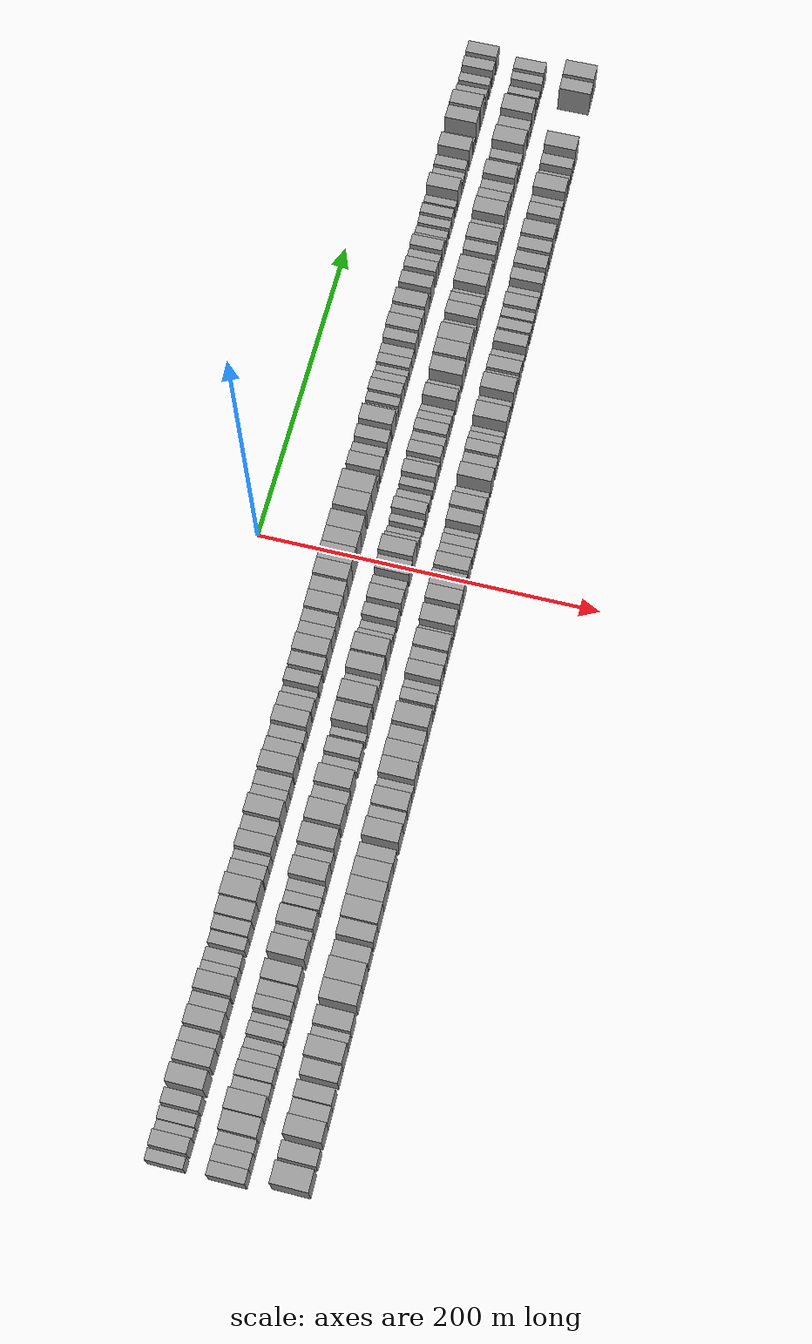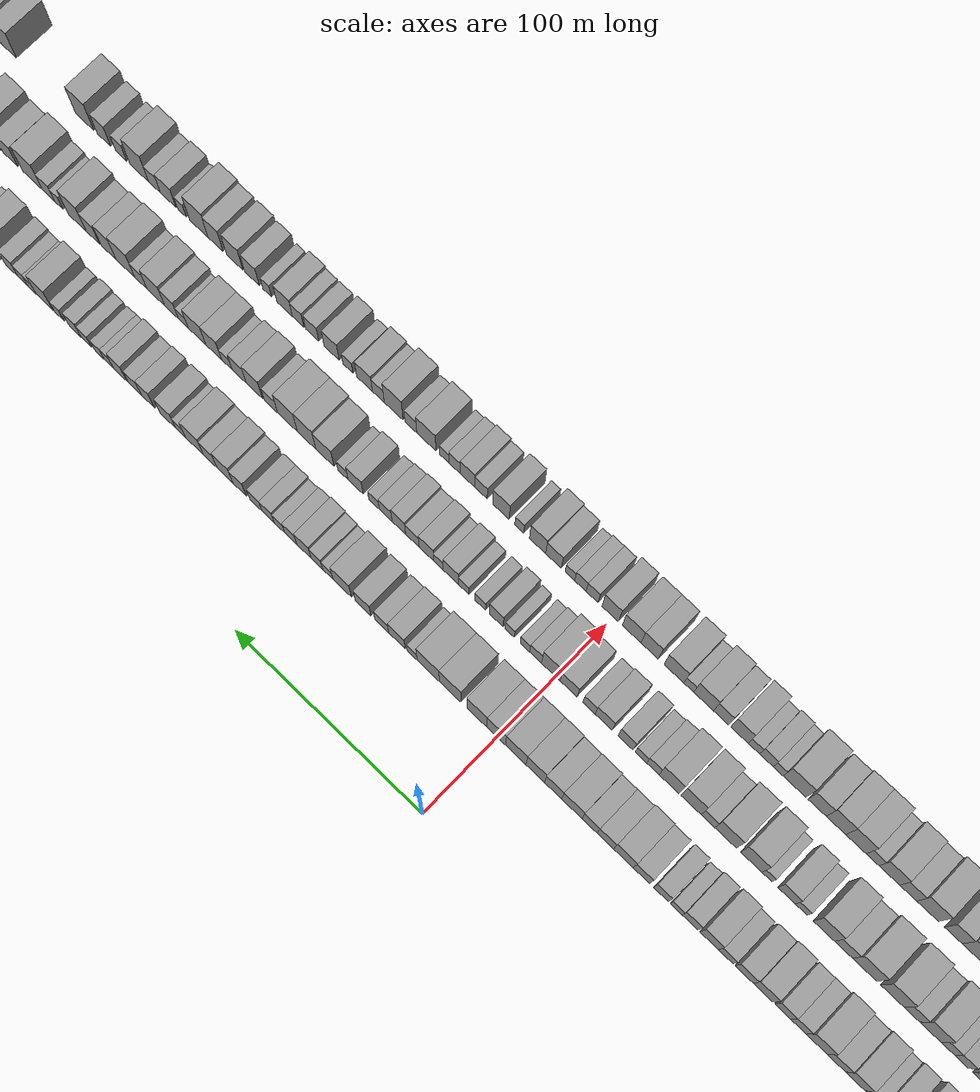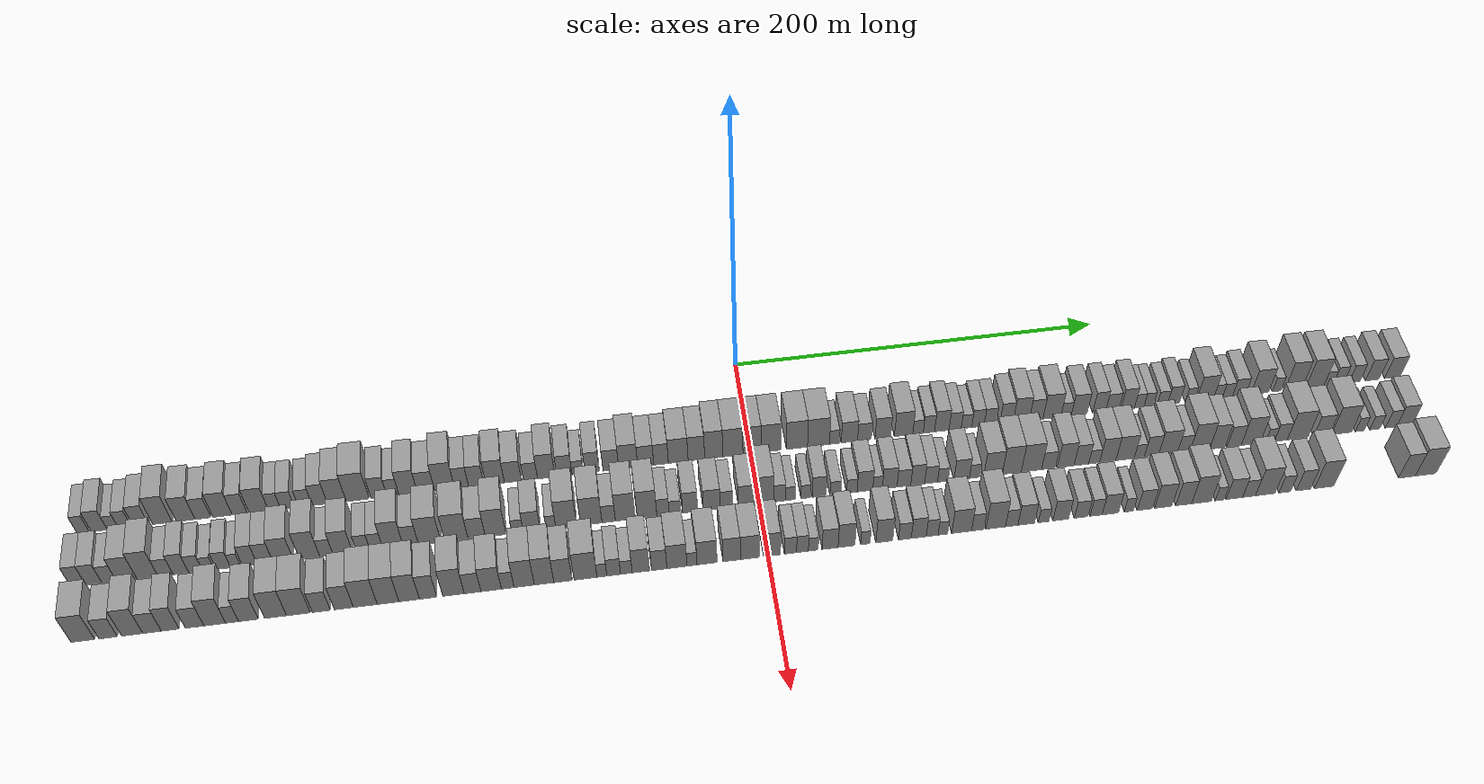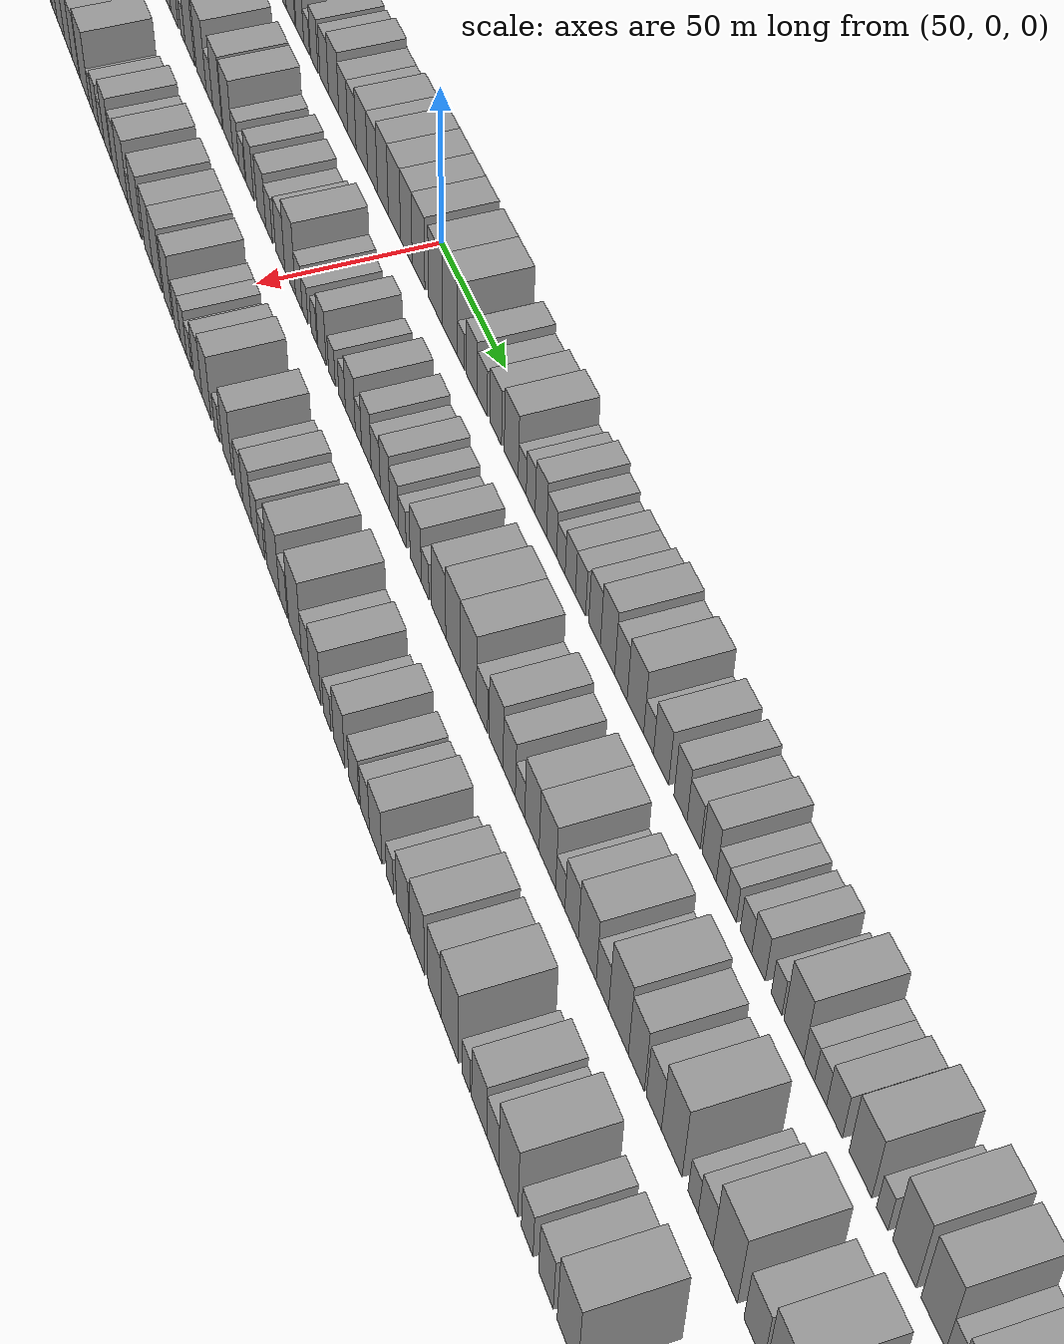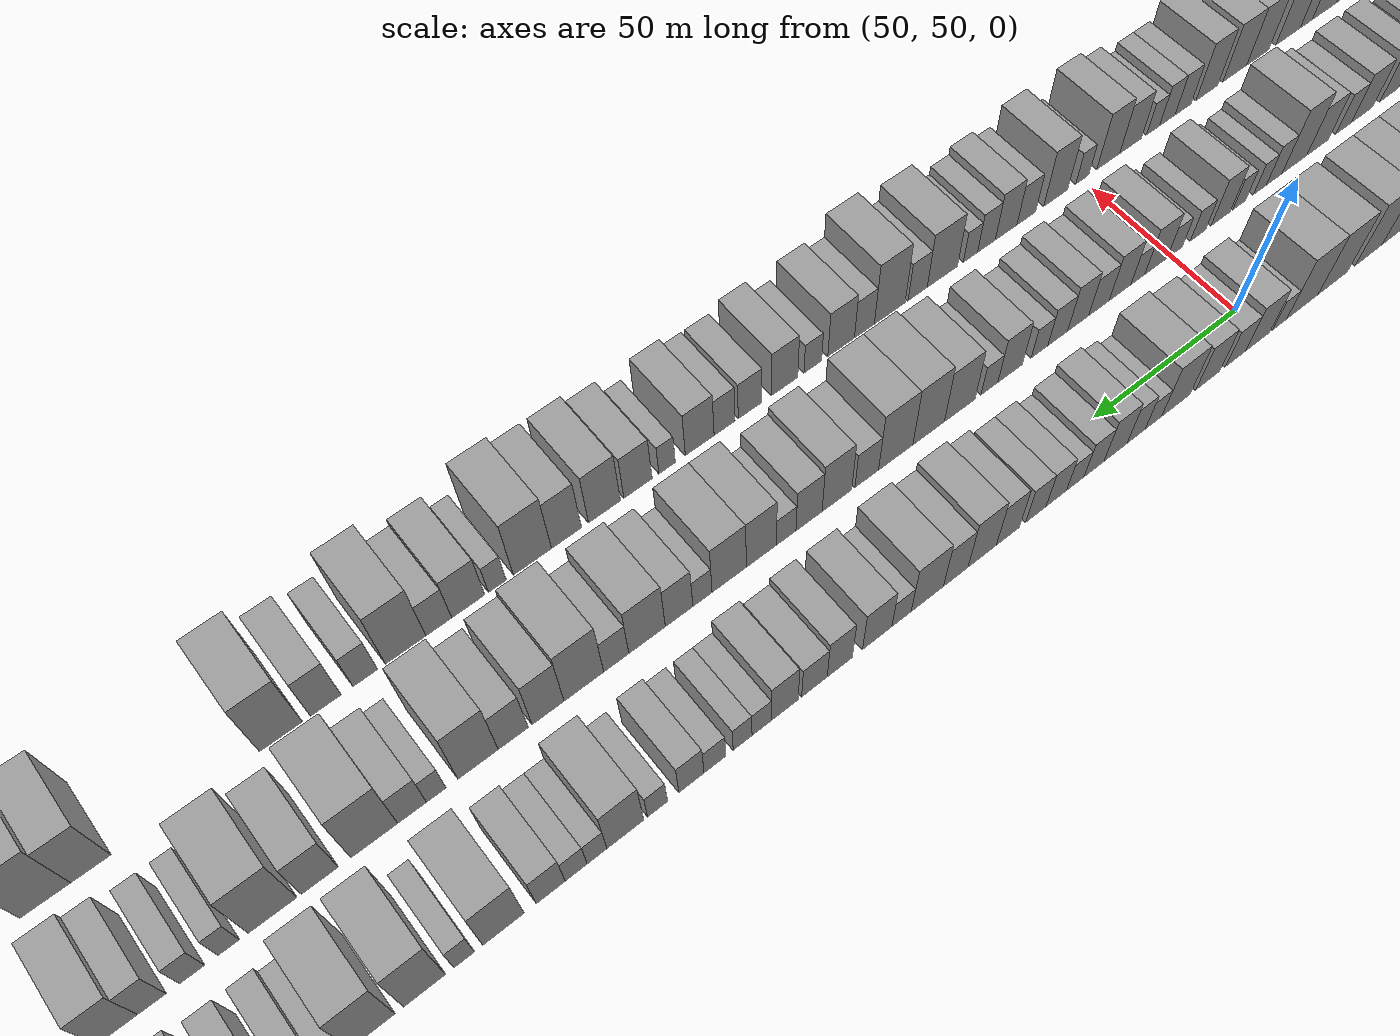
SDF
<sdf version="1.6">
 <world name="default">
  <scene>
   <sky><clouds><speed>12</speed></clouds></sky>
   <ambient>0.4 0.4 0.4 1</ambient>
   <background>0.7 0.7 0.7 1</background>
   <shadows>1</shadows>
  </scene>
  <gravity>0 0 -9.8066</gravity>
  <magnetic_field>6e-06 2.3e-05 -4.2e-05</magnetic_field>
  <physics default="0" name="default_physics" type="ode">
   <ode>
    <solver>
     <type>quick</type>
     <iters>10</iters>
     <sor>1.0</sor>
     <use_dynamic_moi_rescaling>0</use_dynamic_moi_rescaling>
    </solver>
    <constraints>
     <cfm>0</cfm>
     <erp>0.2</erp>
     <contact_max_correcting_vel>100</contact_max_correcting_vel>
     <contact_surface_layer>0.001</contact_surface_layer>
    </constraints>
   </ode>
   <max_step_size>0.004</max_step_size>
   <real_time_factor>1</real_time_factor>
   <real_time_update_rate>250</real_time_update_rate>
  </physics>
  <light name="sun" type="directional">
   <pose>0 0 10 0 0 0</pose>
   <diffuse>0.8 0.8 0.8 1</diffuse>
   <specular>0.2 0.2 0.2 1</specular>
   <attenuation>
    <range>1000</range>
    <constant>0.9</constant>
    <linear>0.01</linear>
    <quadratic>0.001</quadratic>
   </attenuation>
   <direction>-0.5 0.1 -0.9</direction>
  </light>
  <model name="building_1">
   <static>1</static>
   <pose>50.0000 -344.9657 0 0.000000 0.000000 0.000000</pose>
   <link name="link">
    <pose>0 0 7.50 0 0 0</pose>
    <collision name="collision"><geometry><box><size>20.0000 6.0687 15.0000</size></box></geometry></collision>
    <visual name="visual">
     <cast_shadows>0</cast_shadows>
     <geometry><box><size>20.0000 6.0687 15.0000</size></box></geometry>
     <material>
      <script>
       <uri>model://grey_wall/materials/scripts</uri>
       <uri>model://grey_wall/materials/textures</uri>
       <name>vrc/grey_wall</name>
      </script>
     </material>
    </visual>
   </link>
  </model>
  <model name="building_2">
   <static>1</static>
   <pose>50.0000 -336.9161 0 0.000000 0.000000 0.000000</pose>
   <link name="link">
    <pose>0 0 9.00 0 0 0</pose>
    <collision name="collision"><geometry><box><size>20.0000 8.0305 18.0000</size></box></geometry></collision>
    <visual name="visual">
     <cast_shadows>0</cast_shadows>
     <geometry><box><size>20.0000 8.0305 18.0000</size></box></geometry>
     <material>
      <script>
       <uri>model://grey_wall/materials/scripts</uri>
       <uri>model://grey_wall/materials/textures</uri>
       <name>vrc/grey_wall</name>
      </script>
     </material>
    </visual>
   </link>
  </model>
  <model name="building_3">
   <static>1</static>
   <pose>50.0000 -330.0949 0 0.000000 0.000000 0.000000</pose>
   <link name="link">
    <pose>0 0 6.00 0 0 0</pose>
    <collision name="collision"><geometry><box><size>20.0000 5.6119 12.0000</size></box></geometry></collision>
    <visual name="visual">
     <cast_shadows>0</cast_shadows>
     <geometry><box><size>20.0000 5.6119 12.0000</size></box></geometry>
     <material>
      <script>
       <uri>model://grey_wall/materials/scripts</uri>
       <uri>model://grey_wall/materials/textures</uri>
       <name>vrc/grey_wall</name>
      </script>
     </material>
    </visual>
   </link>
  </model>
  <model name="building_4">
   <static>1</static>
   <pose>50.0000 -324.0263 0 0.000000 0.000000 0.000000</pose>
   <link name="link">
    <pose>0 0 7.50 0 0 0</pose>
    <collision name="collision"><geometry><box><size>20.0000 6.5253 15.0000</size></box></geometry></collision>
    <visual name="visual">
     <cast_shadows>0</cast_shadows>
     <geometry><box><size>20.0000 6.5253 15.0000</size></box></geometry>
     <material>
      <script>
       <uri>model://grey_wall/materials/scripts</uri>
       <uri>model://grey_wall/materials/textures</uri>
       <name>vrc/grey_wall</name>
      </script>
     </material>
    </visual>
   </link>
  </model>
  <model name="building_5">
   <static>1</static>
   <pose>50.0000 -315.8973 0 0.000000 0.000000 0.000000</pose>
   <link name="link">
    <pose>0 0 9.00 0 0 0</pose>
    <collision name="collision"><geometry><box><size>20.0000 7.7328 18.0000</size></box></geometry></collision>
    <visual name="visual">
     <cast_shadows>0</cast_shadows>
     <geometry><box><size>20.0000 7.7328 18.0000</size></box></geometry>
     <material>
      <script>
       <uri>model://grey_wall/materials/scripts</uri>
       <uri>model://grey_wall/materials/textures</uri>
       <name>vrc/grey_wall</name>
      </script>
     </material>
    </visual>
   </link>
  </model>
  <model name="building_6">
   <static>1</static>
   <pose>50.0000 -305.1037 0 0.000000 0.000000 0.000000</pose>
   <link name="link">
    <pose>0 0 12.00 0 0 0</pose>
    <collision name="collision"><geometry><box><size>20.0000 9.8543 24.0000</size></box></geometry></collision>
    <visual name="visual">
     <cast_shadows>0</cast_shadows>
     <geometry><box><size>20.0000 9.8543 24.0000</size></box></geometry>
     <material>
      <script>
       <uri>model://grey_wall/materials/scripts</uri>
       <uri>model://grey_wall/materials/textures</uri>
       <name>vrc/grey_wall</name>
      </script>
     </material>
    </visual>
   </link>
  </model>
  <model name="building_7">
   <static>1</static>
   <pose>50.0000 -293.4159 0 0.000000 0.000000 0.000000</pose>
   <link name="link">
    <pose>0 0 10.50 0 0 0</pose>
    <collision name="collision"><geometry><box><size>20.0000 9.5214 21.0000</size></box></geometry></collision>
    <visual name="visual">
     <cast_shadows>0</cast_shadows>
     <geometry><box><size>20.0000 9.5214 21.0000</size></box></geometry>
     <material>
      <script>
       <uri>model://grey_wall/materials/scripts</uri>
       <uri>model://grey_wall/materials/textures</uri>
       <name>vrc/grey_wall</name>
      </script>
     </material>
    </visual>
   </link>
  </model>
  <model name="building_8">
   <static>1</static>
   <pose>50.0000 -284.6538 0 0.000000 0.000000 0.000000</pose>
   <link name="link">
    <pose>0 0 9.00 0 0 0</pose>
    <collision name="collision"><geometry><box><size>20.0000 8.0027 18.0000</size></box></geometry></collision>
    <visual name="visual">
     <cast_shadows>0</cast_shadows>
     <geometry><box><size>20.0000 8.0027 18.0000</size></box></geometry>
     <material>
      <script>
       <uri>model://grey_wall/materials/scripts</uri>
       <uri>model://grey_wall/materials/textures</uri>
       <name>vrc/grey_wall</name>
      </script>
     </material>
    </visual>
   </link>
  </model>
  <model name="building_9">
   <static>1</static>
   <pose>50.0000 -274.7830 0 0.000000 0.000000 0.000000</pose>
   <link name="link">
    <pose>0 0 10.50 0 0 0</pose>
    <collision name="collision"><geometry><box><size>20.0000 9.7389 21.0000</size></box></geometry></collision>
    <visual name="visual">
     <cast_shadows>0</cast_shadows>
     <geometry><box><size>20.0000 9.7389 21.0000</size></box></geometry>
     <material>
      <script>
       <uri>model://grey_wall/materials/scripts</uri>
       <uri>model://grey_wall/materials/textures</uri>
       <name>vrc/grey_wall</name>
      </script>
     </material>
    </visual>
   </link>
  </model>
  <model name="building_10">
   <static>1</static>
   <pose>50.0000 -266.1051 0 0.000000 0.000000 0.000000</pose>
   <link name="link">
    <pose>0 0 9.00 0 0 0</pose>
    <collision name="collision"><geometry><box><size>20.0000 7.6170 18.0000</size></box></geometry></collision>
    <visual name="visual">
     <cast_shadows>0</cast_shadows>
     <geometry><box><size>20.0000 7.6170 18.0000</size></box></geometry>
     <material>
      <script>
       <uri>model://grey_wall/materials/scripts</uri>
       <uri>model://grey_wall/materials/textures</uri>
       <name>vrc/grey_wall</name>
      </script>
     </material>
    </visual>
   </link>
  </model>
  <model name="building_11">
   <static>1</static>
   <pose>50.0000 -256.3716 0 0.000000 0.000000 0.000000</pose>
   <link name="link">
    <pose>0 0 10.50 0 0 0</pose>
    <collision name="collision"><geometry><box><size>20.0000 9.8499 21.0000</size></box></geometry></collision>
    <visual name="visual">
     <cast_shadows>0</cast_shadows>
     <geometry><box><size>20.0000 9.8499 21.0000</size></box></geometry>
     <material>
      <script>
       <uri>model://grey_wall/materials/scripts</uri>
       <uri>model://grey_wall/materials/textures</uri>
       <name>vrc/grey_wall</name>
      </script>
     </material>
    </visual>
   </link>
  </model>
  <model name="building_12">
   <static>1</static>
   <pose>50.0000 -248.3212 0 0.000000 0.000000 0.000000</pose>
   <link name="link">
    <pose>0 0 7.50 0 0 0</pose>
    <collision name="collision"><geometry><box><size>20.0000 6.2508 15.0000</size></box></geometry></collision>
    <visual name="visual">
     <cast_shadows>0</cast_shadows>
     <geometry><box><size>20.0000 6.2508 15.0000</size></box></geometry>
     <material>
      <script>
       <uri>model://grey_wall/materials/scripts</uri>
       <uri>model://grey_wall/materials/textures</uri>
       <name>vrc/grey_wall</name>
      </script>
     </material>
    </visual>
   </link>
  </model>
  <model name="building_13">
   <static>1</static>
   <pose>50.0000 -241.6532 0 0.000000 0.000000 0.000000</pose>
   <link name="link">
    <pose>0 0 7.50 0 0 0</pose>
    <collision name="collision"><geometry><box><size>20.0000 7.0852 15.0000</size></box></geometry></collision>
    <visual name="visual">
     <cast_shadows>0</cast_shadows>
     <geometry><box><size>20.0000 7.0852 15.0000</size></box></geometry>
     <material>
      <script>
       <uri>model://grey_wall/materials/scripts</uri>
       <uri>model://grey_wall/materials/textures</uri>
       <name>vrc/grey_wall</name>
      </script>
     </material>
    </visual>
   </link>
  </model>
  <model name="building_14">
   <static>1</static>
   <pose>50.0000 -232.6272 0 0.000000 0.000000 0.000000</pose>
   <link name="link">
    <pose>0 0 7.50 0 0 0</pose>
    <collision name="collision"><geometry><box><size>20.0000 6.9666 15.0000</size></box></geometry></collision>
    <visual name="visual">
     <cast_shadows>0</cast_shadows>
     <geometry><box><size>20.0000 6.9666 15.0000</size></box></geometry>
     <material>
      <script>
       <uri>model://grey_wall/materials/scripts</uri>
       <uri>model://grey_wall/materials/textures</uri>
       <name>vrc/grey_wall</name>
      </script>
     </material>
    </visual>
   </link>
  </model>
  <model name="building_15">
   <static>1</static>
   <pose>50.0000 -225.2683 0 0.000000 0.000000 0.000000</pose>
   <link name="link">
    <pose>0 0 9.00 0 0 0</pose>
    <collision name="collision"><geometry><box><size>20.0000 7.7513 18.0000</size></box></geometry></collision>
    <visual name="visual">
     <cast_shadows>0</cast_shadows>
     <geometry><box><size>20.0000 7.7513 18.0000</size></box></geometry>
     <material>
      <script>
       <uri>model://grey_wall/materials/scripts</uri>
       <uri>model://grey_wall/materials/textures</uri>
       <name>vrc/grey_wall</name>
      </script>
     </material>
    </visual>
   </link>
  </model>
  <model name="building_16">
   <static>1</static>
   <pose>50.0000 -216.5674 0 0.000000 0.000000 0.000000</pose>
   <link name="link">
    <pose>0 0 10.50 0 0 0</pose>
    <collision name="collision"><geometry><box><size>20.0000 9.6505 21.0000</size></box></geometry></collision>
    <visual name="visual">
     <cast_shadows>0</cast_shadows>
     <geometry><box><size>20.0000 9.6505 21.0000</size></box></geometry>
     <material>
      <script>
       <uri>model://grey_wall/materials/scripts</uri>
       <uri>model://grey_wall/materials/textures</uri>
       <name>vrc/grey_wall</name>
      </script>
     </material>
    </visual>
   </link>
  </model>
  <model name="building_17">
   <static>1</static>
   <pose>50.0000 -205.8485 0 0.000000 0.000000 0.000000</pose>
   <link name="link">
    <pose>0 0 12.00 0 0 0</pose>
    <collision name="collision"><geometry><box><size>20.0000 11.7873 24.0000</size></box></geometry></collision>
    <visual name="visual">
     <cast_shadows>0</cast_shadows>
     <geometry><box><size>20.0000 11.7873 24.0000</size></box></geometry>
     <material>
      <script>
       <uri>model://grey_wall/materials/scripts</uri>
       <uri>model://grey_wall/materials/textures</uri>
       <name>vrc/grey_wall</name>
      </script>
     </material>
    </visual>
   </link>
  </model>
  <model name="building_18">
   <static>1</static>
   <pose>50.0000 -194.8565 0 0.000000 0.000000 0.000000</pose>
   <link name="link">
    <pose>0 0 9.00 0 0 0</pose>
    <collision name="collision"><geometry><box><size>20.0000 8.1968 18.0000</size></box></geometry></collision>
    <visual name="visual">
     <cast_shadows>0</cast_shadows>
     <geometry><box><size>20.0000 8.1968 18.0000</size></box></geometry>
     <material>
      <script>
       <uri>model://grey_wall/materials/scripts</uri>
       <uri>model://grey_wall/materials/textures</uri>
       <name>vrc/grey_wall</name>
      </script>
     </material>
    </visual>
   </link>
  </model>
  <model name="building_19">
   <static>1</static>
   <pose>50.0000 -187.6945 0 0.000000 0.000000 0.000000</pose>
   <link name="link">
    <pose>0 0 7.50 0 0 0</pose>
    <collision name="collision"><geometry><box><size>20.0000 6.1271 15.0000</size></box></geometry></collision>
    <visual name="visual">
     <cast_shadows>0</cast_shadows>
     <geometry><box><size>20.0000 6.1271 15.0000</size></box></geometry>
     <material>
      <script>
       <uri>model://grey_wall/materials/scripts</uri>
       <uri>model://grey_wall/materials/textures</uri>
       <name>vrc/grey_wall</name>
      </script>
     </material>
    </visual>
   </link>
  </model>
  <model name="building_20">
   <static>1</static>
   <pose>50.0000 -179.8617 0 0.000000 0.000000 0.000000</pose>
   <link name="link">
    <pose>0 0 10.50 0 0 0</pose>
    <collision name="collision"><geometry><box><size>20.0000 9.5386 21.0000</size></box></geometry></collision>
    <visual name="visual">
     <cast_shadows>0</cast_shadows>
     <geometry><box><size>20.0000 9.5386 21.0000</size></box></geometry>
     <material>
      <script>
       <uri>model://grey_wall/materials/scripts</uri>
       <uri>model://grey_wall/materials/textures</uri>
       <name>vrc/grey_wall</name>
      </script>
     </material>
    </visual>
   </link>
  </model>
  <model name="building_21">
   <static>1</static>
   <pose>50.0000 -170.6082 0 0.000000 0.000000 0.000000</pose>
   <link name="link">
    <pose>0 0 9.00 0 0 0</pose>
    <collision name="collision"><geometry><box><size>20.0000 8.9684 18.0000</size></box></geometry></collision>
    <visual name="visual">
     <cast_shadows>0</cast_shadows>
     <geometry><box><size>20.0000 8.9684 18.0000</size></box></geometry>
     <material>
      <script>
       <uri>model://grey_wall/materials/scripts</uri>
       <uri>model://grey_wall/materials/textures</uri>
       <name>vrc/grey_wall</name>
      </script>
     </material>
    </visual>
   </link>
  </model>
  <model name="building_22">
   <static>1</static>
   <pose>50.0000 -160.9771 0 0.000000 0.000000 0.000000</pose>
   <link name="link">
    <pose>0 0 12.00 0 0 0</pose>
    <collision name="collision"><geometry><box><size>20.0000 10.2938 24.0000</size></box></geometry></collision>
    <visual name="visual">
     <cast_shadows>0</cast_shadows>
     <geometry><box><size>20.0000 10.2938 24.0000</size></box></geometry>
     <material>
      <script>
       <uri>model://grey_wall/materials/scripts</uri>
       <uri>model://grey_wall/materials/textures</uri>
       <name>vrc/grey_wall</name>
      </script>
     </material>
    </visual>
   </link>
  </model>
  <model name="building_23">
   <static>1</static>
   <pose>50.0000 -152.1624 0 0.000000 0.000000 0.000000</pose>
   <link name="link">
    <pose>0 0 9.00 0 0 0</pose>
    <collision name="collision"><geometry><box><size>20.0000 7.3357 18.0000</size></box></geometry></collision>
    <visual name="visual">
     <cast_shadows>0</cast_shadows>
     <geometry><box><size>20.0000 7.3357 18.0000</size></box></geometry>
     <material>
      <script>
       <uri>model://grey_wall/materials/scripts</uri>
       <uri>model://grey_wall/materials/textures</uri>
       <name>vrc/grey_wall</name>
      </script>
     </material>
    </visual>
   </link>
  </model>
  <model name="building_24">
   <static>1</static>
   <pose>50.0000 -144.5276 0 0.000000 0.000000 0.000000</pose>
   <link name="link">
    <pose>0 0 9.00 0 0 0</pose>
    <collision name="collision"><geometry><box><size>20.0000 7.9338 18.0000</size></box></geometry></collision>
    <visual name="visual">
     <cast_shadows>0</cast_shadows>
     <geometry><box><size>20.0000 7.9338 18.0000</size></box></geometry>
     <material>
      <script>
       <uri>model://grey_wall/materials/scripts</uri>
       <uri>model://grey_wall/materials/textures</uri>
       <name>vrc/grey_wall</name>
      </script>
     </material>
    </visual>
   </link>
  </model>
  <model name="building_25">
   <static>1</static>
   <pose>50.0000 -134.7322 0 0.000000 0.000000 0.000000</pose>
   <link name="link">
    <pose>0 0 10.50 0 0 0</pose>
    <collision name="collision"><geometry><box><size>20.0000 9.6570 21.0000</size></box></geometry></collision>
    <visual name="visual">
     <cast_shadows>0</cast_shadows>
     <geometry><box><size>20.0000 9.6570 21.0000</size></box></geometry>
     <material>
      <script>
       <uri>model://grey_wall/materials/scripts</uri>
       <uri>model://grey_wall/materials/textures</uri>
       <name>vrc/grey_wall</name>
      </script>
     </material>
    </visual>
   </link>
  </model>
  <model name="building_26">
   <static>1</static>
   <pose>50.0000 -125.4382 0 0.000000 0.000000 0.000000</pose>
   <link name="link">
    <pose>0 0 9.00 0 0 0</pose>
    <collision name="collision"><geometry><box><size>20.0000 8.9311 18.0000</size></box></geometry></collision>
    <visual name="visual">
     <cast_shadows>0</cast_shadows>
     <geometry><box><size>20.0000 8.9311 18.0000</size></box></geometry>
     <material>
      <script>
       <uri>model://grey_wall/materials/scripts</uri>
       <uri>model://grey_wall/materials/textures</uri>
       <name>vrc/grey_wall</name>
      </script>
     </material>
    </visual>
   </link>
  </model>
  <model name="building_27">
   <static>1</static>
   <pose>50.0000 -116.3024 0 0.000000 0.000000 0.000000</pose>
   <link name="link">
    <pose>0 0 7.50 0 0 0</pose>
    <collision name="collision"><geometry><box><size>20.0000 7.3405 15.0000</size></box></geometry></collision>
    <visual name="visual">
     <cast_shadows>0</cast_shadows>
     <geometry><box><size>20.0000 7.3405 15.0000</size></box></geometry>
     <material>
      <script>
       <uri>model://grey_wall/materials/scripts</uri>
       <uri>model://grey_wall/materials/textures</uri>
       <name>vrc/grey_wall</name>
      </script>
     </material>
    </visual>
   </link>
  </model>
  <model name="building_28">
   <static>1</static>
   <pose>50.0000 -108.0398 0 0.000000 0.000000 0.000000</pose>
   <link name="link">
    <pose>0 0 10.50 0 0 0</pose>
    <collision name="collision"><geometry><box><size>20.0000 9.1847 21.0000</size></box></geometry></collision>
    <visual name="visual">
     <cast_shadows>0</cast_shadows>
     <geometry><box><size>20.0000 9.1847 21.0000</size></box></geometry>
     <material>
      <script>
       <uri>model://grey_wall/materials/scripts</uri>
       <uri>model://grey_wall/materials/textures</uri>
       <name>vrc/grey_wall</name>
      </script>
     </material>
    </visual>
   </link>
  </model>
  <model name="building_29">
   <static>1</static>
   <pose>50.0000 -98.5034 0 0.000000 0.000000 0.000000</pose>
   <link name="link">
    <pose>0 0 9.00 0 0 0</pose>
    <collision name="collision"><geometry><box><size>20.0000 7.8880 18.0000</size></box></geometry></collision>
    <visual name="visual">
     <cast_shadows>0</cast_shadows>
     <geometry><box><size>20.0000 7.8880 18.0000</size></box></geometry>
     <material>
      <script>
       <uri>model://grey_wall/materials/scripts</uri>
       <uri>model://grey_wall/materials/textures</uri>
       <name>vrc/grey_wall</name>
      </script>
     </material>
    </visual>
   </link>
  </model>
  <model name="building_30">
   <static>1</static>
   <pose>50.0000 -91.6284 0 0.000000 0.000000 0.000000</pose>
   <link name="link">
    <pose>0 0 6.00 0 0 0</pose>
    <collision name="collision"><geometry><box><size>20.0000 5.8620 12.0000</size></box></geometry></collision>
    <visual name="visual">
     <cast_shadows>0</cast_shadows>
     <geometry><box><size>20.0000 5.8620 12.0000</size></box></geometry>
     <material>
      <script>
       <uri>model://grey_wall/materials/scripts</uri>
       <uri>model://grey_wall/materials/textures</uri>
       <name>vrc/grey_wall</name>
      </script>
     </material>
    </visual>
   </link>
  </model>
  <model name="building_31">
   <static>1</static>
   <pose>50.0000 -83.9766 0 0.000000 0.000000 0.000000</pose>
   <link name="link">
    <pose>0 0 9.00 0 0 0</pose>
    <collision name="collision"><geometry><box><size>20.0000 7.4414 18.0000</size></box></geometry></collision>
    <visual name="visual">
     <cast_shadows>0</cast_shadows>
     <geometry><box><size>20.0000 7.4414 18.0000</size></box></geometry>
     <material>
      <script>
       <uri>model://grey_wall/materials/scripts</uri>
       <uri>model://grey_wall/materials/textures</uri>
       <name>vrc/grey_wall</name>
      </script>
     </material>
    </visual>
   </link>
  </model>
  <model name="building_32">
   <static>1</static>
   <pose>50.0000 -74.1132 0 0.000000 0.000000 0.000000</pose>
   <link name="link">
    <pose>0 0 9.00 0 0 0</pose>
    <collision name="collision"><geometry><box><size>20.0000 8.2855 18.0000</size></box></geometry></collision>
    <visual name="visual">
     <cast_shadows>0</cast_shadows>
     <geometry><box><size>20.0000 8.2855 18.0000</size></box></geometry>
     <material>
      <script>
       <uri>model://grey_wall/materials/scripts</uri>
       <uri>model://grey_wall/materials/textures</uri>
       <name>vrc/grey_wall</name>
      </script>
     </material>
    </visual>
   </link>
  </model>
  <model name="building_33">
   <static>1</static>
   <pose>50.0000 -64.9987 0 0.000000 0.000000 0.000000</pose>
   <link name="link">
    <pose>0 0 10.50 0 0 0</pose>
    <collision name="collision"><geometry><box><size>20.0000 9.9436 21.0000</size></box></geometry></collision>
    <visual name="visual">
     <cast_shadows>0</cast_shadows>
     <geometry><box><size>20.0000 9.9436 21.0000</size></box></geometry>
     <material>
      <script>
       <uri>model://grey_wall/materials/scripts</uri>
       <uri>model://grey_wall/materials/textures</uri>
       <name>vrc/grey_wall</name>
      </script>
     </material>
    </visual>
   </link>
  </model>
  <model name="building_34">
   <static>1</static>
   <pose>50.0000 -55.8091 0 0.000000 0.000000 0.000000</pose>
   <link name="link">
    <pose>0 0 9.00 0 0 0</pose>
    <collision name="collision"><geometry><box><size>20.0000 8.4356 18.0000</size></box></geometry></collision>
    <visual name="visual">
     <cast_shadows>0</cast_shadows>
     <geometry><box><size>20.0000 8.4356 18.0000</size></box></geometry>
     <material>
      <script>
       <uri>model://grey_wall/materials/scripts</uri>
       <uri>model://grey_wall/materials/textures</uri>
       <name>vrc/grey_wall</name>
      </script>
     </material>
    </visual>
   </link>
  </model>
  <model name="building_35">
   <static>1</static>
   <pose>50.0000 -47.7244 0 0.000000 0.000000 0.000000</pose>
   <link name="link">
    <pose>0 0 9.00 0 0 0</pose>
    <collision name="collision"><geometry><box><size>20.0000 7.7337 18.0000</size></box></geometry></collision>
    <visual name="visual">
     <cast_shadows>0</cast_shadows>
     <geometry><box><size>20.0000 7.7337 18.0000</size></box></geometry>
     <material>
      <script>
       <uri>model://grey_wall/materials/scripts</uri>
       <uri>model://grey_wall/materials/textures</uri>
       <name>vrc/grey_wall</name>
      </script>
     </material>
    </visual>
   </link>
  </model>
  <model name="building_36">
   <static>1</static>
   <pose>50.0000 -38.6169 0 0.000000 0.000000 0.000000</pose>
   <link name="link">
    <pose>0 0 10.50 0 0 0</pose>
    <collision name="collision"><geometry><box><size>20.0000 10.4813 21.0000</size></box></geometry></collision>
    <visual name="visual">
     <cast_shadows>0</cast_shadows>
     <geometry><box><size>20.0000 10.4813 21.0000</size></box></geometry>
     <material>
      <script>
       <uri>model://grey_wall/materials/scripts</uri>
       <uri>model://grey_wall/materials/textures</uri>
       <name>vrc/grey_wall</name>
      </script>
     </material>
    </visual>
   </link>
  </model>
  <model name="building_37">
   <static>1</static>
   <pose>50.0000 -28.9720 0 0.000000 0.000000 0.000000</pose>
   <link name="link">
    <pose>0 0 10.50 0 0 0</pose>
    <collision name="collision"><geometry><box><size>20.0000 8.8084 21.0000</size></box></geometry></collision>
    <visual name="visual">
     <cast_shadows>0</cast_shadows>
     <geometry><box><size>20.0000 8.8084 21.0000</size></box></geometry>
     <material>
      <script>
       <uri>model://grey_wall/materials/scripts</uri>
       <uri>model://grey_wall/materials/textures</uri>
       <name>vrc/grey_wall</name>
      </script>
     </material>
    </visual>
   </link>
  </model>
  <model name="building_38">
   <static>1</static>
   <pose>50.0000 -19.7284 0 0.000000 0.000000 0.000000</pose>
   <link name="link">
    <pose>0 0 12.00 0 0 0</pose>
    <collision name="collision"><geometry><box><size>20.0000 9.6789 24.0000</size></box></geometry></collision>
    <visual name="visual">
     <cast_shadows>0</cast_shadows>
     <geometry><box><size>20.0000 9.6789 24.0000</size></box></geometry>
     <material>
      <script>
       <uri>model://grey_wall/materials/scripts</uri>
       <uri>model://grey_wall/materials/textures</uri>
       <name>vrc/grey_wall</name>
      </script>
     </material>
    </visual>
   </link>
  </model>
  <model name="building_39">
   <static>1</static>
   <pose>50.0000 -9.5518 0 0.000000 0.000000 0.000000</pose>
   <link name="link">
    <pose>0 0 12.00 0 0 0</pose>
    <collision name="collision"><geometry><box><size>20.0000 10.6742 24.0000</size></box></geometry></collision>
    <visual name="visual">
     <cast_shadows>0</cast_shadows>
     <geometry><box><size>20.0000 10.6742 24.0000</size></box></geometry>
     <material>
      <script>
       <uri>model://grey_wall/materials/scripts</uri>
       <uri>model://grey_wall/materials/textures</uri>
       <name>vrc/grey_wall</name>
      </script>
     </material>
    </visual>
   </link>
  </model>
  <model name="building_40">
   <static>1</static>
   <pose>50.0000 0.6516 0 0.000000 0.000000 0.000000</pose>
   <link name="link">
    <pose>0 0 12.00 0 0 0</pose>
    <collision name="collision"><geometry><box><size>20.0000 9.7326 24.0000</size></box></geometry></collision>
    <visual name="visual">
     <cast_shadows>0</cast_shadows>
     <geometry><box><size>20.0000 9.7326 24.0000</size></box></geometry>
     <material>
      <script>
       <uri>model://grey_wall/materials/scripts</uri>
       <uri>model://grey_wall/materials/textures</uri>
       <name>vrc/grey_wall</name>
      </script>
     </material>
    </visual>
   </link>
  </model>
  <model name="building_41">
   <static>1</static>
   <pose>50.0000 10.7805 0 0.000000 0.000000 0.000000</pose>
   <link name="link">
    <pose>0 0 12.00 0 0 0</pose>
    <collision name="collision"><geometry><box><size>20.0000 10.5251 24.0000</size></box></geometry></collision>
    <visual name="visual">
     <cast_shadows>0</cast_shadows>
     <geometry><box><size>20.0000 10.5251 24.0000</size></box></geometry>
     <material>
      <script>
       <uri>model://grey_wall/materials/scripts</uri>
       <uri>model://grey_wall/materials/textures</uri>
       <name>vrc/grey_wall</name>
      </script>
     </material>
    </visual>
   </link>
  </model>
  <model name="building_42">
   <static>1</static>
   <pose>50.0000 24.7000 0 0.000000 0.000000 0.000000</pose>
   <link name="link">
    <pose>0 0 12.00 0 0 0</pose>
    <collision name="collision"><geometry><box><size>20.0000 11.3139 24.0000</size></box></geometry></collision>
    <visual name="visual">
     <cast_shadows>0</cast_shadows>
     <geometry><box><size>20.0000 11.3139 24.0000</size></box></geometry>
     <material>
      <script>
       <uri>model://grey_wall/materials/scripts</uri>
       <uri>model://grey_wall/materials/textures</uri>
       <name>vrc/grey_wall</name>
      </script>
     </material>
    </visual>
   </link>
  </model>
  <model name="building_43">
   <static>1</static>
   <pose>50.0000 36.2653 0 0.000000 0.000000 0.000000</pose>
   <link name="link">
    <pose>0 0 12.00 0 0 0</pose>
    <collision name="collision"><geometry><box><size>20.0000 11.8165 24.0000</size></box></geometry></collision>
    <visual name="visual">
     <cast_shadows>0</cast_shadows>
     <geometry><box><size>20.0000 11.8165 24.0000</size></box></geometry>
     <material>
      <script>
       <uri>model://grey_wall/materials/scripts</uri>
       <uri>model://grey_wall/materials/textures</uri>
       <name>vrc/grey_wall</name>
      </script>
     </material>
    </visual>
   </link>
  </model>
  <model name="building_44">
   <static>1</static>
   <pose>50.0000 44.8143 0 0.000000 0.000000 0.000000</pose>
   <link name="link">
    <pose>0 0 6.00 0 0 0</pose>
    <collision name="collision"><geometry><box><size>20.0000 5.2817 12.0000</size></box></geometry></collision>
    <visual name="visual">
     <cast_shadows>0</cast_shadows>
     <geometry><box><size>20.0000 5.2817 12.0000</size></box></geometry>
     <material>
      <script>
       <uri>model://grey_wall/materials/scripts</uri>
       <uri>model://grey_wall/materials/textures</uri>
       <name>vrc/grey_wall</name>
      </script>
     </material>
    </visual>
   </link>
  </model>
  <model name="building_45">
   <static>1</static>
   <pose>50.0000 52.8690 0 0.000000 0.000000 0.000000</pose>
   <link name="link">
    <pose>0 0 9.00 0 0 0</pose>
    <collision name="collision"><geometry><box><size>20.0000 8.8278 18.0000</size></box></geometry></collision>
    <visual name="visual">
     <cast_shadows>0</cast_shadows>
     <geometry><box><size>20.0000 8.8278 18.0000</size></box></geometry>
     <material>
      <script>
       <uri>model://grey_wall/materials/scripts</uri>
       <uri>model://grey_wall/materials/textures</uri>
       <name>vrc/grey_wall</name>
      </script>
     </material>
    </visual>
   </link>
  </model>
  <model name="building_46">
   <static>1</static>
   <pose>50.0000 60.9933 0 0.000000 0.000000 0.000000</pose>
   <link name="link">
    <pose>0 0 7.50 0 0 0</pose>
    <collision name="collision"><geometry><box><size>20.0000 7.4207 15.0000</size></box></geometry></collision>
    <visual name="visual">
     <cast_shadows>0</cast_shadows>
     <geometry><box><size>20.0000 7.4207 15.0000</size></box></geometry>
     <material>
      <script>
       <uri>model://grey_wall/materials/scripts</uri>
       <uri>model://grey_wall/materials/textures</uri>
       <name>vrc/grey_wall</name>
      </script>
     </material>
    </visual>
   </link>
  </model>
  <model name="building_47">
   <static>1</static>
   <pose>50.0000 70.9440 0 0.000000 0.000000 0.000000</pose>
   <link name="link">
    <pose>0 0 9.00 0 0 0</pose>
    <collision name="collision"><geometry><box><size>20.0000 8.4807 18.0000</size></box></geometry></collision>
    <visual name="visual">
     <cast_shadows>0</cast_shadows>
     <geometry><box><size>20.0000 8.4807 18.0000</size></box></geometry>
     <material>
      <script>
       <uri>model://grey_wall/materials/scripts</uri>
       <uri>model://grey_wall/materials/textures</uri>
       <name>vrc/grey_wall</name>
      </script>
     </material>
    </visual>
   </link>
  </model>
  <model name="building_48">
   <static>1</static>
   <pose>50.0000 82.1688 0 0.000000 0.000000 0.000000</pose>
   <link name="link">
    <pose>0 0 10.50 0 0 0</pose>
    <collision name="collision"><geometry><box><size>20.0000 9.9690 21.0000</size></box></geometry></collision>
    <visual name="visual">
     <cast_shadows>0</cast_shadows>
     <geometry><box><size>20.0000 9.9690 21.0000</size></box></geometry>
     <material>
      <script>
       <uri>model://grey_wall/materials/scripts</uri>
       <uri>model://grey_wall/materials/textures</uri>
       <name>vrc/grey_wall</name>
      </script>
     </material>
    </visual>
   </link>
  </model>
  <model name="building_49">
   <static>1</static>
   <pose>50.0000 89.9884 0 0.000000 0.000000 0.000000</pose>
   <link name="link">
    <pose>0 0 6.00 0 0 0</pose>
    <collision name="collision"><geometry><box><size>20.0000 5.6702 12.0000</size></box></geometry></collision>
    <visual name="visual">
     <cast_shadows>0</cast_shadows>
     <geometry><box><size>20.0000 5.6702 12.0000</size></box></geometry>
     <material>
      <script>
       <uri>model://grey_wall/materials/scripts</uri>
       <uri>model://grey_wall/materials/textures</uri>
       <name>vrc/grey_wall</name>
      </script>
     </material>
    </visual>
   </link>
  </model>
  <model name="building_50">
   <static>1</static>
   <pose>50.0000 95.9091 0 0.000000 0.000000 0.000000</pose>
   <link name="link">
    <pose>0 0 7.50 0 0 0</pose>
    <collision name="collision"><geometry><box><size>20.0000 6.1710 15.0000</size></box></geometry></collision>
    <visual name="visual">
     <cast_shadows>0</cast_shadows>
     <geometry><box><size>20.0000 6.1710 15.0000</size></box></geometry>
     <material>
      <script>
       <uri>model://grey_wall/materials/scripts</uri>
       <uri>model://grey_wall/materials/textures</uri>
       <name>vrc/grey_wall</name>
      </script>
     </material>
    </visual>
   </link>
  </model>
  <model name="building_51">
   <static>1</static>
   <pose>50.0000 102.9194 0 0.000000 0.000000 0.000000</pose>
   <link name="link">
    <pose>0 0 9.00 0 0 0</pose>
    <collision name="collision"><geometry><box><size>20.0000 7.8496 18.0000</size></box></geometry></collision>
    <visual name="visual">
     <cast_shadows>0</cast_shadows>
     <geometry><box><size>20.0000 7.8496 18.0000</size></box></geometry>
     <material>
      <script>
       <uri>model://grey_wall/materials/scripts</uri>
       <uri>model://grey_wall/materials/textures</uri>
       <name>vrc/grey_wall</name>
      </script>
     </material>
    </visual>
   </link>
  </model>
  <model name="building_52">
   <static>1</static>
   <pose>50.0000 110.1753 0 0.000000 0.000000 0.000000</pose>
   <link name="link">
    <pose>0 0 7.50 0 0 0</pose>
    <collision name="collision"><geometry><box><size>20.0000 6.6623 15.0000</size></box></geometry></collision>
    <visual name="visual">
     <cast_shadows>0</cast_shadows>
     <geometry><box><size>20.0000 6.6623 15.0000</size></box></geometry>
     <material>
      <script>
       <uri>model://grey_wall/materials/scripts</uri>
       <uri>model://grey_wall/materials/textures</uri>
       <name>vrc/grey_wall</name>
      </script>
     </material>
    </visual>
   </link>
  </model>
  <model name="building_53">
   <static>1</static>
   <pose>50.0000 116.3749 0 0.000000 0.000000 0.000000</pose>
   <link name="link">
    <pose>0 0 6.00 0 0 0</pose>
    <collision name="collision"><geometry><box><size>20.0000 5.7369 12.0000</size></box></geometry></collision>
    <visual name="visual">
     <cast_shadows>0</cast_shadows>
     <geometry><box><size>20.0000 5.7369 12.0000</size></box></geometry>
     <material>
      <script>
       <uri>model://grey_wall/materials/scripts</uri>
       <uri>model://grey_wall/materials/textures</uri>
       <name>vrc/grey_wall</name>
      </script>
     </material>
    </visual>
   </link>
  </model>
  <model name="building_54">
   <static>1</static>
   <pose>50.0000 122.5907 0 0.000000 0.000000 0.000000</pose>
   <link name="link">
    <pose>0 0 7.50 0 0 0</pose>
    <collision name="collision"><geometry><box><size>20.0000 6.6947 15.0000</size></box></geometry></collision>
    <visual name="visual">
     <cast_shadows>0</cast_shadows>
     <geometry><box><size>20.0000 6.6947 15.0000</size></box></geometry>
     <material>
      <script>
       <uri>model://grey_wall/materials/scripts</uri>
       <uri>model://grey_wall/materials/textures</uri>
       <name>vrc/grey_wall</name>
      </script>
     </material>
    </visual>
   </link>
  </model>
  <model name="building_55">
   <static>1</static>
   <pose>50.0000 129.2250 0 0.000000 0.000000 0.000000</pose>
   <link name="link">
    <pose>0 0 7.50 0 0 0</pose>
    <collision name="collision"><geometry><box><size>20.0000 6.5739 15.0000</size></box></geometry></collision>
    <visual name="visual">
     <cast_shadows>0</cast_shadows>
     <geometry><box><size>20.0000 6.5739 15.0000</size></box></geometry>
     <material>
      <script>
       <uri>model://grey_wall/materials/scripts</uri>
       <uri>model://grey_wall/materials/textures</uri>
       <name>vrc/grey_wall</name>
      </script>
     </material>
    </visual>
   </link>
  </model>
  <model name="building_56">
   <static>1</static>
   <pose>50.0000 138.1787 0 0.000000 0.000000 0.000000</pose>
   <link name="link">
    <pose>0 0 9.00 0 0 0</pose>
    <collision name="collision"><geometry><box><size>20.0000 7.3336 18.0000</size></box></geometry></collision>
    <visual name="visual">
     <cast_shadows>0</cast_shadows>
     <geometry><box><size>20.0000 7.3336 18.0000</size></box></geometry>
     <material>
      <script>
       <uri>model://grey_wall/materials/scripts</uri>
       <uri>model://grey_wall/materials/textures</uri>
       <name>vrc/grey_wall</name>
      </script>
     </material>
    </visual>
   </link>
  </model>
  <model name="building_57">
   <static>1</static>
   <pose>50.0000 146.2890 0 0.000000 0.000000 0.000000</pose>
   <link name="link">
    <pose>0 0 10.50 0 0 0</pose>
    <collision name="collision"><geometry><box><size>20.0000 8.8871 21.0000</size></box></geometry></collision>
    <visual name="visual">
     <cast_shadows>0</cast_shadows>
     <geometry><box><size>20.0000 8.8871 21.0000</size></box></geometry>
     <material>
      <script>
       <uri>model://grey_wall/materials/scripts</uri>
       <uri>model://grey_wall/materials/textures</uri>
       <name>vrc/grey_wall</name>
      </script>
     </material>
    </visual>
   </link>
  </model>
  <model name="building_58">
   <static>1</static>
   <pose>50.0000 154.5236 0 0.000000 0.000000 0.000000</pose>
   <link name="link">
    <pose>0 0 9.00 0 0 0</pose>
    <collision name="collision"><geometry><box><size>20.0000 7.5820 18.0000</size></box></geometry></collision>
    <visual name="visual">
     <cast_shadows>0</cast_shadows>
     <geometry><box><size>20.0000 7.5820 18.0000</size></box></geometry>
     <material>
      <script>
       <uri>model://grey_wall/materials/scripts</uri>
       <uri>model://grey_wall/materials/textures</uri>
       <name>vrc/grey_wall</name>
      </script>
     </material>
    </visual>
   </link>
  </model>
  <model name="building_59">
   <static>1</static>
   <pose>50.0000 163.2395 0 0.000000 0.000000 0.000000</pose>
   <link name="link">
    <pose>0 0 10.50 0 0 0</pose>
    <collision name="collision"><geometry><box><size>20.0000 9.8498 21.0000</size></box></geometry></collision>
    <visual name="visual">
     <cast_shadows>0</cast_shadows>
     <geometry><box><size>20.0000 9.8498 21.0000</size></box></geometry>
     <material>
      <script>
       <uri>model://grey_wall/materials/scripts</uri>
       <uri>model://grey_wall/materials/textures</uri>
       <name>vrc/grey_wall</name>
      </script>
     </material>
    </visual>
   </link>
  </model>
  <model name="building_60">
   <static>1</static>
   <pose>50.0000 171.0696 0 0.000000 0.000000 0.000000</pose>
   <link name="link">
    <pose>0 0 6.00 0 0 0</pose>
    <collision name="collision"><geometry><box><size>20.0000 5.8104 12.0000</size></box></geometry></collision>
    <visual name="visual">
     <cast_shadows>0</cast_shadows>
     <geometry><box><size>20.0000 5.8104 12.0000</size></box></geometry>
     <material>
      <script>
       <uri>model://grey_wall/materials/scripts</uri>
       <uri>model://grey_wall/materials/textures</uri>
       <name>vrc/grey_wall</name>
      </script>
     </material>
    </visual>
   </link>
  </model>
  <model name="building_61">
   <static>1</static>
   <pose>50.0000 178.3178 0 0.000000 0.000000 0.000000</pose>
   <link name="link">
    <pose>0 0 9.00 0 0 0</pose>
    <collision name="collision"><geometry><box><size>20.0000 8.6861 18.0000</size></box></geometry></collision>
    <visual name="visual">
     <cast_shadows>0</cast_shadows>
     <geometry><box><size>20.0000 8.6861 18.0000</size></box></geometry>
     <material>
      <script>
       <uri>model://grey_wall/materials/scripts</uri>
       <uri>model://grey_wall/materials/textures</uri>
       <name>vrc/grey_wall</name>
      </script>
     </material>
    </visual>
   </link>
  </model>
  <model name="building_62">
   <static>1</static>
   <pose>50.0000 189.3022 0 0.000000 0.000000 0.000000</pose>
   <link name="link">
    <pose>0 0 9.00 0 0 0</pose>
    <collision name="collision"><geometry><box><size>20.0000 7.2827 18.0000</size></box></geometry></collision>
    <visual name="visual">
     <cast_shadows>0</cast_shadows>
     <geometry><box><size>20.0000 7.2827 18.0000</size></box></geometry>
     <material>
      <script>
       <uri>model://grey_wall/materials/scripts</uri>
       <uri>model://grey_wall/materials/textures</uri>
       <name>vrc/grey_wall</name>
      </script>
     </material>
    </visual>
   </link>
  </model>
  <model name="building_63">
   <static>1</static>
   <pose>50.0000 196.6041 0 0.000000 0.000000 0.000000</pose>
   <link name="link">
    <pose>0 0 7.50 0 0 0</pose>
    <collision name="collision"><geometry><box><size>20.0000 7.3212 15.0000</size></box></geometry></collision>
    <visual name="visual">
     <cast_shadows>0</cast_shadows>
     <geometry><box><size>20.0000 7.3212 15.0000</size></box></geometry>
     <material>
      <script>
       <uri>model://grey_wall/materials/scripts</uri>
       <uri>model://grey_wall/materials/textures</uri>
       <name>vrc/grey_wall</name>
      </script>
     </material>
    </visual>
   </link>
  </model>
  <model name="building_64">
   <static>1</static>
   <pose>50.0000 205.0572 0 0.000000 0.000000 0.000000</pose>
   <link name="link">
    <pose>0 0 9.00 0 0 0</pose>
    <collision name="collision"><geometry><box><size>20.0000 7.5849 18.0000</size></box></geometry></collision>
    <visual name="visual">
     <cast_shadows>0</cast_shadows>
     <geometry><box><size>20.0000 7.5849 18.0000</size></box></geometry>
     <material>
      <script>
       <uri>model://grey_wall/materials/scripts</uri>
       <uri>model://grey_wall/materials/textures</uri>
       <name>vrc/grey_wall</name>
      </script>
     </material>
    </visual>
   </link>
  </model>
  <model name="building_65">
   <static>1</static>
   <pose>50.0000 211.5247 0 0.000000 0.000000 0.000000</pose>
   <link name="link">
    <pose>0 0 6.00 0 0 0</pose>
    <collision name="collision"><geometry><box><size>20.0000 5.3502 12.0000</size></box></geometry></collision>
    <visual name="visual">
     <cast_shadows>0</cast_shadows>
     <geometry><box><size>20.0000 5.3502 12.0000</size></box></geometry>
     <material>
      <script>
       <uri>model://grey_wall/materials/scripts</uri>
       <uri>model://grey_wall/materials/textures</uri>
       <name>vrc/grey_wall</name>
      </script>
     </material>
    </visual>
   </link>
  </model>
  <model name="building_66">
   <static>1</static>
   <pose>50.0000 216.8057 0 0.000000 0.000000 0.000000</pose>
   <link name="link">
    <pose>0 0 6.00 0 0 0</pose>
    <collision name="collision"><geometry><box><size>20.0000 5.2118 12.0000</size></box></geometry></collision>
    <visual name="visual">
     <cast_shadows>0</cast_shadows>
     <geometry><box><size>20.0000 5.2118 12.0000</size></box></geometry>
     <material>
      <script>
       <uri>model://grey_wall/materials/scripts</uri>
       <uri>model://grey_wall/materials/textures</uri>
       <name>vrc/grey_wall</name>
      </script>
     </material>
    </visual>
   </link>
  </model>
  <model name="building_67">
   <static>1</static>
   <pose>50.0000 224.3799 0 0.000000 0.000000 0.000000</pose>
   <link name="link">
    <pose>0 0 6.00 0 0 0</pose>
    <collision name="collision"><geometry><box><size>20.0000 5.9366 12.0000</size></box></geometry></collision>
    <visual name="visual">
     <cast_shadows>0</cast_shadows>
     <geometry><box><size>20.0000 5.9366 12.0000</size></box></geometry>
     <material>
      <script>
       <uri>model://grey_wall/materials/scripts</uri>
       <uri>model://grey_wall/materials/textures</uri>
       <name>vrc/grey_wall</name>
      </script>
     </material>
    </visual>
   </link>
  </model>
  <model name="building_68">
   <static>1</static>
   <pose>50.0000 230.7400 0 0.000000 0.000000 0.000000</pose>
   <link name="link">
    <pose>0 0 7.50 0 0 0</pose>
    <collision name="collision"><geometry><box><size>20.0000 6.7836 15.0000</size></box></geometry></collision>
    <visual name="visual">
     <cast_shadows>0</cast_shadows>
     <geometry><box><size>20.0000 6.7836 15.0000</size></box></geometry>
     <material>
      <script>
       <uri>model://grey_wall/materials/scripts</uri>
       <uri>model://grey_wall/materials/textures</uri>
       <name>vrc/grey_wall</name>
      </script>
     </material>
    </visual>
   </link>
  </model>
  <model name="building_69">
   <static>1</static>
   <pose>50.0000 239.7752 0 0.000000 0.000000 0.000000</pose>
   <link name="link">
    <pose>0 0 6.00 0 0 0</pose>
    <collision name="collision"><geometry><box><size>20.0000 5.2867 12.0000</size></box></geometry></collision>
    <visual name="visual">
     <cast_shadows>0</cast_shadows>
     <geometry><box><size>20.0000 5.2867 12.0000</size></box></geometry>
     <material>
      <script>
       <uri>model://grey_wall/materials/scripts</uri>
       <uri>model://grey_wall/materials/textures</uri>
       <name>vrc/grey_wall</name>
      </script>
     </material>
    </visual>
   </link>
  </model>
  <model name="building_70">
   <static>1</static>
   <pose>50.0000 248.2243 0 0.000000 0.000000 0.000000</pose>
   <link name="link">
    <pose>0 0 10.50 0 0 0</pose>
    <collision name="collision"><geometry><box><size>20.0000 9.6114 21.0000</size></box></geometry></collision>
    <visual name="visual">
     <cast_shadows>0</cast_shadows>
     <geometry><box><size>20.0000 9.6114 21.0000</size></box></geometry>
     <material>
      <script>
       <uri>model://grey_wall/materials/scripts</uri>
       <uri>model://grey_wall/materials/textures</uri>
       <name>vrc/grey_wall</name>
      </script>
     </material>
    </visual>
   </link>
  </model>
  <model name="building_71">
   <static>1</static>
   <pose>50.0000 255.5449 0 0.000000 0.000000 0.000000</pose>
   <link name="link">
    <pose>0 0 6.00 0 0 0</pose>
    <collision name="collision"><geometry><box><size>20.0000 5.0299 12.0000</size></box></geometry></collision>
    <visual name="visual">
     <cast_shadows>0</cast_shadows>
     <geometry><box><size>20.0000 5.0299 12.0000</size></box></geometry>
     <material>
      <script>
       <uri>model://grey_wall/materials/scripts</uri>
       <uri>model://grey_wall/materials/textures</uri>
       <name>vrc/grey_wall</name>
      </script>
     </material>
    </visual>
   </link>
  </model>
  <model name="building_72">
   <static>1</static>
   <pose>50.0000 260.8522 0 0.000000 0.000000 0.000000</pose>
   <link name="link">
    <pose>0 0 6.00 0 0 0</pose>
    <collision name="collision"><geometry><box><size>20.0000 5.5846 12.0000</size></box></geometry></collision>
    <visual name="visual">
     <cast_shadows>0</cast_shadows>
     <geometry><box><size>20.0000 5.5846 12.0000</size></box></geometry>
     <material>
      <script>
       <uri>model://grey_wall/materials/scripts</uri>
       <uri>model://grey_wall/materials/textures</uri>
       <name>vrc/grey_wall</name>
      </script>
     </material>
    </visual>
   </link>
  </model>
  <model name="building_73">
   <static>1</static>
   <pose>50.0000 267.2864 0 0.000000 0.000000 0.000000</pose>
   <link name="link">
    <pose>0 0 7.50 0 0 0</pose>
    <collision name="collision"><geometry><box><size>20.0000 7.2839 15.0000</size></box></geometry></collision>
    <visual name="visual">
     <cast_shadows>0</cast_shadows>
     <geometry><box><size>20.0000 7.2839 15.0000</size></box></geometry>
     <material>
      <script>
       <uri>model://grey_wall/materials/scripts</uri>
       <uri>model://grey_wall/materials/textures</uri>
       <name>vrc/grey_wall</name>
      </script>
     </material>
    </visual>
   </link>
  </model>
  <model name="building_74">
   <static>1</static>
   <pose>50.0000 278.9940 0 0.000000 0.000000 0.000000</pose>
   <link name="link">
    <pose>0 0 10.50 0 0 0</pose>
    <collision name="collision"><geometry><box><size>20.0000 10.1313 21.0000</size></box></geometry></collision>
    <visual name="visual">
     <cast_shadows>0</cast_shadows>
     <geometry><box><size>20.0000 10.1313 21.0000</size></box></geometry>
     <material>
      <script>
       <uri>model://grey_wall/materials/scripts</uri>
       <uri>model://grey_wall/materials/textures</uri>
       <name>vrc/grey_wall</name>
      </script>
     </material>
    </visual>
   </link>
  </model>
  <model name="building_75">
   <static>1</static>
   <pose>50.0000 288.5395 0 0.000000 0.000000 0.000000</pose>
   <link name="link">
    <pose>0 0 6.00 0 0 0</pose>
    <collision name="collision"><geometry><box><size>20.0000 4.9599 12.0000</size></box></geometry></collision>
    <visual name="visual">
     <cast_shadows>0</cast_shadows>
     <geometry><box><size>20.0000 4.9599 12.0000</size></box></geometry>
     <material>
      <script>
       <uri>model://grey_wall/materials/scripts</uri>
       <uri>model://grey_wall/materials/textures</uri>
       <name>vrc/grey_wall</name>
      </script>
     </material>
    </visual>
   </link>
  </model>
  <model name="building_76">
   <static>1</static>
   <pose>50.0000 297.9738 0 0.000000 0.000000 0.000000</pose>
   <link name="link">
    <pose>0 0 12.00 0 0 0</pose>
    <collision name="collision"><geometry><box><size>20.0000 9.9086 24.0000</size></box></geometry></collision>
    <visual name="visual">
     <cast_shadows>0</cast_shadows>
     <geometry><box><size>20.0000 9.9086 24.0000</size></box></geometry>
     <material>
      <script>
       <uri>model://grey_wall/materials/scripts</uri>
       <uri>model://grey_wall/materials/textures</uri>
       <name>vrc/grey_wall</name>
      </script>
     </material>
    </visual>
   </link>
  </model>
  <model name="building_77">
   <static>1</static>
   <pose>50.0000 310.0574 0 0.000000 0.000000 0.000000</pose>
   <link name="link">
    <pose>0 0 12.00 0 0 0</pose>
    <collision name="collision"><geometry><box><size>20.0000 10.2586 24.0000</size></box></geometry></collision>
    <visual name="visual">
     <cast_shadows>0</cast_shadows>
     <geometry><box><size>20.0000 10.2586 24.0000</size></box></geometry>
     <material>
      <script>
       <uri>model://grey_wall/materials/scripts</uri>
       <uri>model://grey_wall/materials/textures</uri>
       <name>vrc/grey_wall</name>
      </script>
     </material>
    </visual>
   </link>
  </model>
  <model name="building_78">
   <static>1</static>
   <pose>50.0000 317.7867 0 0.000000 0.000000 0.000000</pose>
   <link name="link">
    <pose>0 0 6.00 0 0 0</pose>
    <collision name="collision"><geometry><box><size>20.0000 5.2000 12.0000</size></box></geometry></collision>
    <visual name="visual">
     <cast_shadows>0</cast_shadows>
     <geometry><box><size>20.0000 5.2000 12.0000</size></box></geometry>
     <material>
      <script>
       <uri>model://grey_wall/materials/scripts</uri>
       <uri>model://grey_wall/materials/textures</uri>
       <name>vrc/grey_wall</name>
      </script>
     </material>
    </visual>
   </link>
  </model>
  <model name="building_79">
   <static>1</static>
   <pose>50.0000 323.3931 0 0.000000 0.000000 0.000000</pose>
   <link name="link">
    <pose>0 0 7.50 0 0 0</pose>
    <collision name="collision"><geometry><box><size>20.0000 6.0129 15.0000</size></box></geometry></collision>
    <visual name="visual">
     <cast_shadows>0</cast_shadows>
     <geometry><box><size>20.0000 6.0129 15.0000</size></box></geometry>
     <material>
      <script>
       <uri>model://grey_wall/materials/scripts</uri>
       <uri>model://grey_wall/materials/textures</uri>
       <name>vrc/grey_wall</name>
      </script>
     </material>
    </visual>
   </link>
  </model>
  <model name="building_80">
   <static>1</static>
   <pose>50.0000 332.5935 0 0.000000 0.000000 0.000000</pose>
   <link name="link">
    <pose>0 0 7.50 0 0 0</pose>
    <collision name="collision"><geometry><box><size>20.0000 6.3878 15.0000</size></box></geometry></collision>
    <visual name="visual">
     <cast_shadows>0</cast_shadows>
     <geometry><box><size>20.0000 6.3878 15.0000</size></box></geometry>
     <material>
      <script>
       <uri>model://grey_wall/materials/scripts</uri>
       <uri>model://grey_wall/materials/textures</uri>
       <name>vrc/grey_wall</name>
      </script>
     </material>
    </visual>
   </link>
  </model>
  <model name="building_81">
   <static>1</static>
   <pose>50.0000 342.7441 0 0.000000 0.000000 0.000000</pose>
   <link name="link">
    <pose>0 0 9.00 0 0 0</pose>
    <collision name="collision"><geometry><box><size>20.0000 7.9135 18.0000</size></box></geometry></collision>
    <visual name="visual">
     <cast_shadows>0</cast_shadows>
     <geometry><box><size>20.0000 7.9135 18.0000</size></box></geometry>
     <material>
      <script>
       <uri>model://grey_wall/materials/scripts</uri>
       <uri>model://grey_wall/materials/textures</uri>
       <name>vrc/grey_wall</name>
      </script>
     </material>
    </visual>
   </link>
  </model>
  <model name="building_82">
   <static>1</static>
   <pose>50.0000 354.1689 0 0.000000 0.000000 0.000000</pose>
   <link name="link">
    <pose>0 0 9.00 0 0 0</pose>
    <collision name="collision"><geometry><box><size>20.0000 8.9360 18.0000</size></box></geometry></collision>
    <visual name="visual">
     <cast_shadows>0</cast_shadows>
     <geometry><box><size>20.0000 8.9360 18.0000</size></box></geometry>
     <material>
      <script>
       <uri>model://grey_wall/materials/scripts</uri>
       <uri>model://grey_wall/materials/textures</uri>
       <name>vrc/grey_wall</name>
      </script>
     </material>
    </visual>
   </link>
  </model>
  <model name="building_83">
   <static>1</static>
   <pose>82.0000 -344.3608 0 0.000000 0.000000 0.000000</pose>
   <link name="link">
    <pose>0 0 9.00 0 0 0</pose>
    <collision name="collision"><geometry><box><size>20.0000 7.2784 18.0000</size></box></geometry></collision>
    <visual name="visual">
     <cast_shadows>0</cast_shadows>
     <geometry><box><size>20.0000 7.2784 18.0000</size></box></geometry>
     <material>
      <script>
       <uri>model://grey_wall/materials/scripts</uri>
       <uri>model://grey_wall/materials/textures</uri>
       <name>vrc/grey_wall</name>
      </script>
     </material>
    </visual>
   </link>
  </model>
  <model name="building_84">
   <static>1</static>
   <pose>82.0000 -336.7660 0 0.000000 0.000000 0.000000</pose>
   <link name="link">
    <pose>0 0 9.00 0 0 0</pose>
    <collision name="collision"><geometry><box><size>20.0000 7.9110 18.0000</size></box></geometry></collision>
    <visual name="visual">
     <cast_shadows>0</cast_shadows>
     <geometry><box><size>20.0000 7.9110 18.0000</size></box></geometry>
     <material>
      <script>
       <uri>model://grey_wall/materials/scripts</uri>
       <uri>model://grey_wall/materials/textures</uri>
       <name>vrc/grey_wall</name>
      </script>
     </material>
    </visual>
   </link>
  </model>
  <model name="building_85">
   <static>1</static>
   <pose>82.0000 -329.2255 0 0.000000 0.000000 0.000000</pose>
   <link name="link">
    <pose>0 0 7.50 0 0 0</pose>
    <collision name="collision"><geometry><box><size>20.0000 7.1701 15.0000</size></box></geometry></collision>
    <visual name="visual">
     <cast_shadows>0</cast_shadows>
     <geometry><box><size>20.0000 7.1701 15.0000</size></box></geometry>
     <material>
      <script>
       <uri>model://grey_wall/materials/scripts</uri>
       <uri>model://grey_wall/materials/textures</uri>
       <name>vrc/grey_wall</name>
      </script>
     </material>
    </visual>
   </link>
  </model>
  <model name="building_86">
   <static>1</static>
   <pose>82.0000 -320.6686 0 0.000000 0.000000 0.000000</pose>
   <link name="link">
    <pose>0 0 10.50 0 0 0</pose>
    <collision name="collision"><geometry><box><size>20.0000 9.9436 21.0000</size></box></geometry></collision>
    <visual name="visual">
     <cast_shadows>0</cast_shadows>
     <geometry><box><size>20.0000 9.9436 21.0000</size></box></geometry>
     <material>
      <script>
       <uri>model://grey_wall/materials/scripts</uri>
       <uri>model://grey_wall/materials/textures</uri>
       <name>vrc/grey_wall</name>
      </script>
     </material>
    </visual>
   </link>
  </model>
  <model name="building_87">
   <static>1</static>
   <pose>82.0000 -310.5000 0 0.000000 0.000000 0.000000</pose>
   <link name="link">
    <pose>0 0 12.00 0 0 0</pose>
    <collision name="collision"><geometry><box><size>20.0000 10.3937 24.0000</size></box></geometry></collision>
    <visual name="visual">
     <cast_shadows>0</cast_shadows>
     <geometry><box><size>20.0000 10.3937 24.0000</size></box></geometry>
     <material>
      <script>
       <uri>model://grey_wall/materials/scripts</uri>
       <uri>model://grey_wall/materials/textures</uri>
       <name>vrc/grey_wall</name>
      </script>
     </material>
    </visual>
   </link>
  </model>
  <model name="building_88">
   <static>1</static>
   <pose>82.0000 -301.5817 0 0.000000 0.000000 0.000000</pose>
   <link name="link">
    <pose>0 0 7.50 0 0 0</pose>
    <collision name="collision"><geometry><box><size>20.0000 7.4429 15.0000</size></box></geometry></collision>
    <visual name="visual">
     <cast_shadows>0</cast_shadows>
     <geometry><box><size>20.0000 7.4429 15.0000</size></box></geometry>
     <material>
      <script>
       <uri>model://grey_wall/materials/scripts</uri>
       <uri>model://grey_wall/materials/textures</uri>
       <name>vrc/grey_wall</name>
      </script>
     </material>
    </visual>
   </link>
  </model>
  <model name="building_89">
   <static>1</static>
   <pose>82.0000 -294.0032 0 0.000000 0.000000 0.000000</pose>
   <link name="link">
    <pose>0 0 9.00 0 0 0</pose>
    <collision name="collision"><geometry><box><size>20.0000 7.7140 18.0000</size></box></geometry></collision>
    <visual name="visual">
     <cast_shadows>0</cast_shadows>
     <geometry><box><size>20.0000 7.7140 18.0000</size></box></geometry>
     <material>
      <script>
       <uri>model://grey_wall/materials/scripts</uri>
       <uri>model://grey_wall/materials/textures</uri>
       <name>vrc/grey_wall</name>
      </script>
     </material>
    </visual>
   </link>
  </model>
  <model name="building_90">
   <static>1</static>
   <pose>82.0000 -286.6773 0 0.000000 0.000000 0.000000</pose>
   <link name="link">
    <pose>0 0 7.50 0 0 0</pose>
    <collision name="collision"><geometry><box><size>20.0000 6.9378 15.0000</size></box></geometry></collision>
    <visual name="visual">
     <cast_shadows>0</cast_shadows>
     <geometry><box><size>20.0000 6.9378 15.0000</size></box></geometry>
     <material>
      <script>
       <uri>model://grey_wall/materials/scripts</uri>
       <uri>model://grey_wall/materials/textures</uri>
       <name>vrc/grey_wall</name>
      </script>
     </material>
    </visual>
   </link>
  </model>
  <model name="building_91">
   <static>1</static>
   <pose>82.0000 -280.3136 0 0.000000 0.000000 0.000000</pose>
   <link name="link">
    <pose>0 0 6.00 0 0 0</pose>
    <collision name="collision"><geometry><box><size>20.0000 5.7896 12.0000</size></box></geometry></collision>
    <visual name="visual">
     <cast_shadows>0</cast_shadows>
     <geometry><box><size>20.0000 5.7896 12.0000</size></box></geometry>
     <material>
      <script>
       <uri>model://grey_wall/materials/scripts</uri>
       <uri>model://grey_wall/materials/textures</uri>
       <name>vrc/grey_wall</name>
      </script>
     </material>
    </visual>
   </link>
  </model>
  <model name="building_92">
   <static>1</static>
   <pose>82.0000 -272.9134 0 0.000000 0.000000 0.000000</pose>
   <link name="link">
    <pose>0 0 7.50 0 0 0</pose>
    <collision name="collision"><geometry><box><size>20.0000 7.0108 15.0000</size></box></geometry></collision>
    <visual name="visual">
     <cast_shadows>0</cast_shadows>
     <geometry><box><size>20.0000 7.0108 15.0000</size></box></geometry>
     <material>
      <script>
       <uri>model://grey_wall/materials/scripts</uri>
       <uri>model://grey_wall/materials/textures</uri>
       <name>vrc/grey_wall</name>
      </script>
     </material>
    </visual>
   </link>
  </model>
  <model name="building_93">
   <static>1</static>
   <pose>82.0000 -266.8978 0 0.000000 0.000000 0.000000</pose>
   <link name="link">
    <pose>0 0 6.00 0 0 0</pose>
    <collision name="collision"><geometry><box><size>20.0000 5.0204 12.0000</size></box></geometry></collision>
    <visual name="visual">
     <cast_shadows>0</cast_shadows>
     <geometry><box><size>20.0000 5.0204 12.0000</size></box></geometry>
     <material>
      <script>
       <uri>model://grey_wall/materials/scripts</uri>
       <uri>model://grey_wall/materials/textures</uri>
       <name>vrc/grey_wall</name>
      </script>
     </material>
    </visual>
   </link>
  </model>
  <model name="building_94">
   <static>1</static>
   <pose>82.0000 -259.7431 0 0.000000 0.000000 0.000000</pose>
   <link name="link">
    <pose>0 0 9.00 0 0 0</pose>
    <collision name="collision"><geometry><box><size>20.0000 7.2891 18.0000</size></box></geometry></collision>
    <visual name="visual">
     <cast_shadows>0</cast_shadows>
     <geometry><box><size>20.0000 7.2891 18.0000</size></box></geometry>
     <material>
      <script>
       <uri>model://grey_wall/materials/scripts</uri>
       <uri>model://grey_wall/materials/textures</uri>
       <name>vrc/grey_wall</name>
      </script>
     </material>
    </visual>
   </link>
  </model>
  <model name="building_95">
   <static>1</static>
   <pose>82.0000 -252.1448 0 0.000000 0.000000 0.000000</pose>
   <link name="link">
    <pose>0 0 9.00 0 0 0</pose>
    <collision name="collision"><geometry><box><size>20.0000 7.9074 18.0000</size></box></geometry></collision>
    <visual name="visual">
     <cast_shadows>0</cast_shadows>
     <geometry><box><size>20.0000 7.9074 18.0000</size></box></geometry>
     <material>
      <script>
       <uri>model://grey_wall/materials/scripts</uri>
       <uri>model://grey_wall/materials/textures</uri>
       <name>vrc/grey_wall</name>
      </script>
     </material>
    </visual>
   </link>
  </model>
  <model name="building_96">
   <static>1</static>
   <pose>82.0000 -243.1355 0 0.000000 0.000000 0.000000</pose>
   <link name="link">
    <pose>0 0 10.50 0 0 0</pose>
    <collision name="collision"><geometry><box><size>20.0000 10.1112 21.0000</size></box></geometry></collision>
    <visual name="visual">
     <cast_shadows>0</cast_shadows>
     <geometry><box><size>20.0000 10.1112 21.0000</size></box></geometry>
     <material>
      <script>
       <uri>model://grey_wall/materials/scripts</uri>
       <uri>model://grey_wall/materials/textures</uri>
       <name>vrc/grey_wall</name>
      </script>
     </material>
    </visual>
   </link>
  </model>
  <model name="building_97">
   <static>1</static>
   <pose>82.0000 -230.0014 0 0.000000 0.000000 0.000000</pose>
   <link name="link">
    <pose>0 0 12.00 0 0 0</pose>
    <collision name="collision"><geometry><box><size>20.0000 10.1570 24.0000</size></box></geometry></collision>
    <visual name="visual">
     <cast_shadows>0</cast_shadows>
     <geometry><box><size>20.0000 10.1570 24.0000</size></box></geometry>
     <material>
      <script>
       <uri>model://grey_wall/materials/scripts</uri>
       <uri>model://grey_wall/materials/textures</uri>
       <name>vrc/grey_wall</name>
      </script>
     </material>
    </visual>
   </link>
  </model>
  <model name="building_98">
   <static>1</static>
   <pose>82.0000 -221.5478 0 0.000000 0.000000 0.000000</pose>
   <link name="link">
    <pose>0 0 7.50 0 0 0</pose>
    <collision name="collision"><geometry><box><size>20.0000 6.7502 15.0000</size></box></geometry></collision>
    <visual name="visual">
     <cast_shadows>0</cast_shadows>
     <geometry><box><size>20.0000 6.7502 15.0000</size></box></geometry>
     <material>
      <script>
       <uri>model://grey_wall/materials/scripts</uri>
       <uri>model://grey_wall/materials/textures</uri>
       <name>vrc/grey_wall</name>
      </script>
     </material>
    </visual>
   </link>
  </model>
  <model name="building_99">
   <static>1</static>
   <pose>82.0000 -213.2766 0 0.000000 0.000000 0.000000</pose>
   <link name="link">
    <pose>0 0 10.50 0 0 0</pose>
    <collision name="collision"><geometry><box><size>20.0000 9.7922 21.0000</size></box></geometry></collision>
    <visual name="visual">
     <cast_shadows>0</cast_shadows>
     <geometry><box><size>20.0000 9.7922 21.0000</size></box></geometry>
     <material>
      <script>
       <uri>model://grey_wall/materials/scripts</uri>
       <uri>model://grey_wall/materials/textures</uri>
       <name>vrc/grey_wall</name>
      </script>
     </material>
    </visual>
   </link>
  </model>
  <model name="building_100">
   <static>1</static>
   <pose>82.0000 -203.0173 0 0.000000 0.000000 0.000000</pose>
   <link name="link">
    <pose>0 0 7.50 0 0 0</pose>
    <collision name="collision"><geometry><box><size>20.0000 6.7264 15.0000</size></box></geometry></collision>
    <visual name="visual">
     <cast_shadows>0</cast_shadows>
     <geometry><box><size>20.0000 6.7264 15.0000</size></box></geometry>
     <material>
      <script>
       <uri>model://grey_wall/materials/scripts</uri>
       <uri>model://grey_wall/materials/textures</uri>
       <name>vrc/grey_wall</name>
      </script>
     </material>
    </visual>
   </link>
  </model>
  <model name="building_101">
   <static>1</static>
   <pose>82.0000 -196.3740 0 0.000000 0.000000 0.000000</pose>
   <link name="link">
    <pose>0 0 7.50 0 0 0</pose>
    <collision name="collision"><geometry><box><size>20.0000 6.5601 15.0000</size></box></geometry></collision>
    <visual name="visual">
     <cast_shadows>0</cast_shadows>
     <geometry><box><size>20.0000 6.5601 15.0000</size></box></geometry>
     <material>
      <script>
       <uri>model://grey_wall/materials/scripts</uri>
       <uri>model://grey_wall/materials/textures</uri>
       <name>vrc/grey_wall</name>
      </script>
     </material>
    </visual>
   </link>
  </model>
  <model name="building_102">
   <static>1</static>
   <pose>82.0000 -187.9912 0 0.000000 0.000000 0.000000</pose>
   <link name="link">
    <pose>0 0 12.00 0 0 0</pose>
    <collision name="collision"><geometry><box><size>20.0000 10.2055 24.0000</size></box></geometry></collision>
    <visual name="visual">
     <cast_shadows>0</cast_shadows>
     <geometry><box><size>20.0000 10.2055 24.0000</size></box></geometry>
     <material>
      <script>
       <uri>model://grey_wall/materials/scripts</uri>
       <uri>model://grey_wall/materials/textures</uri>
       <name>vrc/grey_wall</name>
      </script>
     </material>
    </visual>
   </link>
  </model>
  <model name="building_103">
   <static>1</static>
   <pose>82.0000 -179.0582 0 0.000000 0.000000 0.000000</pose>
   <link name="link">
    <pose>0 0 9.00 0 0 0</pose>
    <collision name="collision"><geometry><box><size>20.0000 7.6605 18.0000</size></box></geometry></collision>
    <visual name="visual">
     <cast_shadows>0</cast_shadows>
     <geometry><box><size>20.0000 7.6605 18.0000</size></box></geometry>
     <material>
      <script>
       <uri>model://grey_wall/materials/scripts</uri>
       <uri>model://grey_wall/materials/textures</uri>
       <name>vrc/grey_wall</name>
      </script>
     </material>
    </visual>
   </link>
  </model>
  <model name="building_104">
   <static>1</static>
   <pose>82.0000 -169.5747 0 0.000000 0.000000 0.000000</pose>
   <link name="link">
    <pose>0 0 12.00 0 0 0</pose>
    <collision name="collision"><geometry><box><size>20.0000 11.3066 24.0000</size></box></geometry></collision>
    <visual name="visual">
     <cast_shadows>0</cast_shadows>
     <geometry><box><size>20.0000 11.3066 24.0000</size></box></geometry>
     <material>
      <script>
       <uri>model://grey_wall/materials/scripts</uri>
       <uri>model://grey_wall/materials/textures</uri>
       <name>vrc/grey_wall</name>
      </script>
     </material>
    </visual>
   </link>
  </model>
  <model name="building_105">
   <static>1</static>
   <pose>82.0000 -156.0349 0 0.000000 0.000000 0.000000</pose>
   <link name="link">
    <pose>0 0 12.00 0 0 0</pose>
    <collision name="collision"><geometry><box><size>20.0000 11.7731 24.0000</size></box></geometry></collision>
    <visual name="visual">
     <cast_shadows>0</cast_shadows>
     <geometry><box><size>20.0000 11.7731 24.0000</size></box></geometry>
     <material>
      <script>
       <uri>model://grey_wall/materials/scripts</uri>
       <uri>model://grey_wall/materials/textures</uri>
       <name>vrc/grey_wall</name>
      </script>
     </material>
    </visual>
   </link>
  </model>
  <model name="building_106">
   <static>1</static>
   <pose>82.0000 -145.7401 0 0.000000 0.000000 0.000000</pose>
   <link name="link">
    <pose>0 0 9.00 0 0 0</pose>
    <collision name="collision"><geometry><box><size>20.0000 8.8165 18.0000</size></box></geometry></collision>
    <visual name="visual">
     <cast_shadows>0</cast_shadows>
     <geometry><box><size>20.0000 8.8165 18.0000</size></box></geometry>
     <material>
      <script>
       <uri>model://grey_wall/materials/scripts</uri>
       <uri>model://grey_wall/materials/textures</uri>
       <name>vrc/grey_wall</name>
      </script>
     </material>
    </visual>
   </link>
  </model>
  <model name="building_107">
   <static>1</static>
   <pose>82.0000 -136.0598 0 0.000000 0.000000 0.000000</pose>
   <link name="link">
    <pose>0 0 12.00 0 0 0</pose>
    <collision name="collision"><geometry><box><size>20.0000 10.5439 24.0000</size></box></geometry></collision>
    <visual name="visual">
     <cast_shadows>0</cast_shadows>
     <geometry><box><size>20.0000 10.5439 24.0000</size></box></geometry>
     <material>
      <script>
       <uri>model://grey_wall/materials/scripts</uri>
       <uri>model://grey_wall/materials/textures</uri>
       <name>vrc/grey_wall</name>
      </script>
     </material>
    </visual>
   </link>
  </model>
  <model name="building_108">
   <static>1</static>
   <pose>82.0000 -124.8444 0 0.000000 0.000000 0.000000</pose>
   <link name="link">
    <pose>0 0 6.00 0 0 0</pose>
    <collision name="collision"><geometry><box><size>20.0000 5.8870 12.0000</size></box></geometry></collision>
    <visual name="visual">
     <cast_shadows>0</cast_shadows>
     <geometry><box><size>20.0000 5.8870 12.0000</size></box></geometry>
     <material>
      <script>
       <uri>model://grey_wall/materials/scripts</uri>
       <uri>model://grey_wall/materials/textures</uri>
       <name>vrc/grey_wall</name>
      </script>
     </material>
    </visual>
   </link>
  </model>
  <model name="building_109">
   <static>1</static>
   <pose>82.0000 -117.5791 0 0.000000 0.000000 0.000000</pose>
   <link name="link">
    <pose>0 0 9.00 0 0 0</pose>
    <collision name="collision"><geometry><box><size>20.0000 8.6437 18.0000</size></box></geometry></collision>
    <visual name="visual">
     <cast_shadows>0</cast_shadows>
     <geometry><box><size>20.0000 8.6437 18.0000</size></box></geometry>
     <material>
      <script>
       <uri>model://grey_wall/materials/scripts</uri>
       <uri>model://grey_wall/materials/textures</uri>
       <name>vrc/grey_wall</name>
      </script>
     </material>
    </visual>
   </link>
  </model>
  <model name="building_110">
   <static>1</static>
   <pose>82.0000 -107.7934 0 0.000000 0.000000 0.000000</pose>
   <link name="link">
    <pose>0 0 6.00 0 0 0</pose>
    <collision name="collision"><geometry><box><size>20.0000 4.9277 12.0000</size></box></geometry></collision>
    <visual name="visual">
     <cast_shadows>0</cast_shadows>
     <geometry><box><size>20.0000 4.9277 12.0000</size></box></geometry>
     <material>
      <script>
       <uri>model://grey_wall/materials/scripts</uri>
       <uri>model://grey_wall/materials/textures</uri>
       <name>vrc/grey_wall</name>
      </script>
     </material>
    </visual>
   </link>
  </model>
  <model name="building_111">
   <static>1</static>
   <pose>82.0000 -99.9474 0 0.000000 0.000000 0.000000</pose>
   <link name="link">
    <pose>0 0 12.00 0 0 0</pose>
    <collision name="collision"><geometry><box><size>20.0000 10.7643 24.0000</size></box></geometry></collision>
    <visual name="visual">
     <cast_shadows>0</cast_shadows>
     <geometry><box><size>20.0000 10.7643 24.0000</size></box></geometry>
     <material>
      <script>
       <uri>model://grey_wall/materials/scripts</uri>
       <uri>model://grey_wall/materials/textures</uri>
       <name>vrc/grey_wall</name>
      </script>
     </material>
    </visual>
   </link>
  </model>
  <model name="building_112">
   <static>1</static>
   <pose>82.0000 -87.1145 0 0.000000 0.000000 0.000000</pose>
   <link name="link">
    <pose>0 0 12.00 0 0 0</pose>
    <collision name="collision"><geometry><box><size>20.0000 10.9016 24.0000</size></box></geometry></collision>
    <visual name="visual">
     <cast_shadows>0</cast_shadows>
     <geometry><box><size>20.0000 10.9016 24.0000</size></box></geometry>
     <material>
      <script>
       <uri>model://grey_wall/materials/scripts</uri>
       <uri>model://grey_wall/materials/textures</uri>
       <name>vrc/grey_wall</name>
      </script>
     </material>
    </visual>
   </link>
  </model>
  <model name="building_113">
   <static>1</static>
   <pose>82.0000 -78.2129 0 0.000000 0.000000 0.000000</pose>
   <link name="link">
    <pose>0 0 7.50 0 0 0</pose>
    <collision name="collision"><geometry><box><size>20.0000 6.9017 15.0000</size></box></geometry></collision>
    <visual name="visual">
     <cast_shadows>0</cast_shadows>
     <geometry><box><size>20.0000 6.9017 15.0000</size></box></geometry>
     <material>
      <script>
       <uri>model://grey_wall/materials/scripts</uri>
       <uri>model://grey_wall/materials/textures</uri>
       <name>vrc/grey_wall</name>
      </script>
     </material>
    </visual>
   </link>
  </model>
  <model name="building_114">
   <static>1</static>
   <pose>82.0000 -69.6232 0 0.000000 0.000000 0.000000</pose>
   <link name="link">
    <pose>0 0 12.00 0 0 0</pose>
    <collision name="collision"><geometry><box><size>20.0000 10.2777 24.0000</size></box></geometry></collision>
    <visual name="visual">
     <cast_shadows>0</cast_shadows>
     <geometry><box><size>20.0000 10.2777 24.0000</size></box></geometry>
     <material>
      <script>
       <uri>model://grey_wall/materials/scripts</uri>
       <uri>model://grey_wall/materials/textures</uri>
       <name>vrc/grey_wall</name>
      </script>
     </material>
    </visual>
   </link>
  </model>
  <model name="building_115">
   <static>1</static>
   <pose>82.0000 -58.4166 0 0.000000 0.000000 0.000000</pose>
   <link name="link">
    <pose>0 0 12.00 0 0 0</pose>
    <collision name="collision"><geometry><box><size>20.0000 10.1355 24.0000</size></box></geometry></collision>
    <visual name="visual">
     <cast_shadows>0</cast_shadows>
     <geometry><box><size>20.0000 10.1355 24.0000</size></box></geometry>
     <material>
      <script>
       <uri>model://grey_wall/materials/scripts</uri>
       <uri>model://grey_wall/materials/textures</uri>
       <name>vrc/grey_wall</name>
      </script>
     </material>
    </visual>
   </link>
  </model>
  <model name="building_116">
   <static>1</static>
   <pose>82.0000 -50.1716 0 0.000000 0.000000 0.000000</pose>
   <link name="link">
    <pose>0 0 7.50 0 0 0</pose>
    <collision name="collision"><geometry><box><size>20.0000 6.3544 15.0000</size></box></geometry></collision>
    <visual name="visual">
     <cast_shadows>0</cast_shadows>
     <geometry><box><size>20.0000 6.3544 15.0000</size></box></geometry>
     <material>
      <script>
       <uri>model://grey_wall/materials/scripts</uri>
       <uri>model://grey_wall/materials/textures</uri>
       <name>vrc/grey_wall</name>
      </script>
     </material>
    </visual>
   </link>
  </model>
  <model name="building_117">
   <static>1</static>
   <pose>82.0000 -44.0033 0 0.000000 0.000000 0.000000</pose>
   <link name="link">
    <pose>0 0 6.00 0 0 0</pose>
    <collision name="collision"><geometry><box><size>20.0000 5.9822 12.0000</size></box></geometry></collision>
    <visual name="visual">
     <cast_shadows>0</cast_shadows>
     <geometry><box><size>20.0000 5.9822 12.0000</size></box></geometry>
     <material>
      <script>
       <uri>model://grey_wall/materials/scripts</uri>
       <uri>model://grey_wall/materials/textures</uri>
       <name>vrc/grey_wall</name>
      </script>
     </material>
    </visual>
   </link>
  </model>
  <model name="building_118">
   <static>1</static>
   <pose>82.0000 -36.1231 0 0.000000 0.000000 0.000000</pose>
   <link name="link">
    <pose>0 0 9.00 0 0 0</pose>
    <collision name="collision"><geometry><box><size>20.0000 7.7782 18.0000</size></box></geometry></collision>
    <visual name="visual">
     <cast_shadows>0</cast_shadows>
     <geometry><box><size>20.0000 7.7782 18.0000</size></box></geometry>
     <material>
      <script>
       <uri>model://grey_wall/materials/scripts</uri>
       <uri>model://grey_wall/materials/textures</uri>
       <name>vrc/grey_wall</name>
      </script>
     </material>
    </visual>
   </link>
  </model>
  <model name="building_119">
   <static>1</static>
   <pose>82.0000 -24.8423 0 0.000000 0.000000 0.000000</pose>
   <link name="link">
    <pose>0 0 9.00 0 0 0</pose>
    <collision name="collision"><geometry><box><size>20.0000 8.7834 18.0000</size></box></geometry></collision>
    <visual name="visual">
     <cast_shadows>0</cast_shadows>
     <geometry><box><size>20.0000 8.7834 18.0000</size></box></geometry>
     <material>
      <script>
       <uri>model://grey_wall/materials/scripts</uri>
       <uri>model://grey_wall/materials/textures</uri>
       <name>vrc/grey_wall</name>
      </script>
     </material>
    </visual>
   </link>
  </model>
  <model name="building_120">
   <static>1</static>
   <pose>82.0000 -17.2281 0 0.000000 0.000000 0.000000</pose>
   <link name="link">
    <pose>0 0 7.50 0 0 0</pose>
    <collision name="collision"><geometry><box><size>20.0000 6.4450 15.0000</size></box></geometry></collision>
    <visual name="visual">
     <cast_shadows>0</cast_shadows>
     <geometry><box><size>20.0000 6.4450 15.0000</size></box></geometry>
     <material>
      <script>
       <uri>model://grey_wall/materials/scripts</uri>
       <uri>model://grey_wall/materials/textures</uri>
       <name>vrc/grey_wall</name>
      </script>
     </material>
    </visual>
   </link>
  </model>
  <model name="building_121">
   <static>1</static>
   <pose>82.0000 -6.6397 0 0.000000 0.000000 0.000000</pose>
   <link name="link">
    <pose>0 0 9.00 0 0 0</pose>
    <collision name="collision"><geometry><box><size>20.0000 8.7318 18.0000</size></box></geometry></collision>
    <visual name="visual">
     <cast_shadows>0</cast_shadows>
     <geometry><box><size>20.0000 8.7318 18.0000</size></box></geometry>
     <material>
      <script>
       <uri>model://grey_wall/materials/scripts</uri>
       <uri>model://grey_wall/materials/textures</uri>
       <name>vrc/grey_wall</name>
      </script>
     </material>
    </visual>
   </link>
  </model>
  <model name="building_122">
   <static>1</static>
   <pose>82.0000 2.6378 0 0.000000 0.000000 0.000000</pose>
   <link name="link">
    <pose>0 0 12.00 0 0 0</pose>
    <collision name="collision"><geometry><box><size>20.0000 9.8232 24.0000</size></box></geometry></collision>
    <visual name="visual">
     <cast_shadows>0</cast_shadows>
     <geometry><box><size>20.0000 9.8232 24.0000</size></box></geometry>
     <material>
      <script>
       <uri>model://grey_wall/materials/scripts</uri>
       <uri>model://grey_wall/materials/textures</uri>
       <name>vrc/grey_wall</name>
      </script>
     </material>
    </visual>
   </link>
  </model>
  <model name="building_123">
   <static>1</static>
   <pose>82.0000 10.6384 0 0.000000 0.000000 0.000000</pose>
   <link name="link">
    <pose>0 0 7.50 0 0 0</pose>
    <collision name="collision"><geometry><box><size>20.0000 6.1781 15.0000</size></box></geometry></collision>
    <visual name="visual">
     <cast_shadows>0</cast_shadows>
     <geometry><box><size>20.0000 6.1781 15.0000</size></box></geometry>
     <material>
      <script>
       <uri>model://grey_wall/materials/scripts</uri>
       <uri>model://grey_wall/materials/textures</uri>
       <name>vrc/grey_wall</name>
      </script>
     </material>
    </visual>
   </link>
  </model>
  <model name="building_124">
   <static>1</static>
   <pose>82.0000 16.2486 0 0.000000 0.000000 0.000000</pose>
   <link name="link">
    <pose>0 0 6.00 0 0 0</pose>
    <collision name="collision"><geometry><box><size>20.0000 5.0421 12.0000</size></box></geometry></collision>
    <visual name="visual">
     <cast_shadows>0</cast_shadows>
     <geometry><box><size>20.0000 5.0421 12.0000</size></box></geometry>
     <material>
      <script>
       <uri>model://grey_wall/materials/scripts</uri>
       <uri>model://grey_wall/materials/textures</uri>
       <name>vrc/grey_wall</name>
      </script>
     </material>
    </visual>
   </link>
  </model>
  <model name="building_125">
   <static>1</static>
   <pose>82.0000 24.2443 0 0.000000 0.000000 0.000000</pose>
   <link name="link">
    <pose>0 0 6.00 0 0 0</pose>
    <collision name="collision"><geometry><box><size>20.0000 4.9494 12.0000</size></box></geometry></collision>
    <visual name="visual">
     <cast_shadows>0</cast_shadows>
     <geometry><box><size>20.0000 4.9494 12.0000</size></box></geometry>
     <material>
      <script>
       <uri>model://grey_wall/materials/scripts</uri>
       <uri>model://grey_wall/materials/textures</uri>
       <name>vrc/grey_wall</name>
      </script>
     </material>
    </visual>
   </link>
  </model>
  <model name="building_126">
   <static>1</static>
   <pose>82.0000 31.3654 0 0.000000 0.000000 0.000000</pose>
   <link name="link">
    <pose>0 0 9.00 0 0 0</pose>
    <collision name="collision"><geometry><box><size>20.0000 7.2928 18.0000</size></box></geometry></collision>
    <visual name="visual">
     <cast_shadows>0</cast_shadows>
     <geometry><box><size>20.0000 7.2928 18.0000</size></box></geometry>
     <material>
      <script>
       <uri>model://grey_wall/materials/scripts</uri>
       <uri>model://grey_wall/materials/textures</uri>
       <name>vrc/grey_wall</name>
      </script>
     </material>
    </visual>
   </link>
  </model>
  <model name="building_127">
   <static>1</static>
   <pose>82.0000 39.8989 0 0.000000 0.000000 0.000000</pose>
   <link name="link">
    <pose>0 0 6.00 0 0 0</pose>
    <collision name="collision"><geometry><box><size>20.0000 5.7742 12.0000</size></box></geometry></collision>
    <visual name="visual">
     <cast_shadows>0</cast_shadows>
     <geometry><box><size>20.0000 5.7742 12.0000</size></box></geometry>
     <material>
      <script>
       <uri>model://grey_wall/materials/scripts</uri>
       <uri>model://grey_wall/materials/textures</uri>
       <name>vrc/grey_wall</name>
      </script>
     </material>
    </visual>
   </link>
  </model>
  <model name="building_128">
   <static>1</static>
   <pose>82.0000 48.5575 0 0.000000 0.000000 0.000000</pose>
   <link name="link">
    <pose>0 0 6.00 0 0 0</pose>
    <collision name="collision"><geometry><box><size>20.0000 5.5428 12.0000</size></box></geometry></collision>
    <visual name="visual">
     <cast_shadows>0</cast_shadows>
     <geometry><box><size>20.0000 5.5428 12.0000</size></box></geometry>
     <material>
      <script>
       <uri>model://grey_wall/materials/scripts</uri>
       <uri>model://grey_wall/materials/textures</uri>
       <name>vrc/grey_wall</name>
      </script>
     </material>
    </visual>
   </link>
  </model>
  <model name="building_129">
   <static>1</static>
   <pose>82.0000 55.4622 0 0.000000 0.000000 0.000000</pose>
   <link name="link">
    <pose>0 0 9.00 0 0 0</pose>
    <collision name="collision"><geometry><box><size>20.0000 8.2667 18.0000</size></box></geometry></collision>
    <visual name="visual">
     <cast_shadows>0</cast_shadows>
     <geometry><box><size>20.0000 8.2667 18.0000</size></box></geometry>
     <material>
      <script>
       <uri>model://grey_wall/materials/scripts</uri>
       <uri>model://grey_wall/materials/textures</uri>
       <name>vrc/grey_wall</name>
      </script>
     </material>
    </visual>
   </link>
  </model>
  <model name="building_130">
   <static>1</static>
   <pose>82.0000 62.1192 0 0.000000 0.000000 0.000000</pose>
   <link name="link">
    <pose>0 0 6.00 0 0 0</pose>
    <collision name="collision"><geometry><box><size>20.0000 5.0472 12.0000</size></box></geometry></collision>
    <visual name="visual">
     <cast_shadows>0</cast_shadows>
     <geometry><box><size>20.0000 5.0472 12.0000</size></box></geometry>
     <material>
      <script>
       <uri>model://grey_wall/materials/scripts</uri>
       <uri>model://grey_wall/materials/textures</uri>
       <name>vrc/grey_wall</name>
      </script>
     </material>
    </visual>
   </link>
  </model>
  <model name="building_131">
   <static>1</static>
   <pose>82.0000 68.5437 0 0.000000 0.000000 0.000000</pose>
   <link name="link">
    <pose>0 0 9.00 0 0 0</pose>
    <collision name="collision"><geometry><box><size>20.0000 7.8018 18.0000</size></box></geometry></collision>
    <visual name="visual">
     <cast_shadows>0</cast_shadows>
     <geometry><box><size>20.0000 7.8018 18.0000</size></box></geometry>
     <material>
      <script>
       <uri>model://grey_wall/materials/scripts</uri>
       <uri>model://grey_wall/materials/textures</uri>
       <name>vrc/grey_wall</name>
      </script>
     </material>
    </visual>
   </link>
  </model>
  <model name="building_132">
   <static>1</static>
   <pose>82.0000 76.0768 0 0.000000 0.000000 0.000000</pose>
   <link name="link">
    <pose>0 0 7.50 0 0 0</pose>
    <collision name="collision"><geometry><box><size>20.0000 7.2645 15.0000</size></box></geometry></collision>
    <visual name="visual">
     <cast_shadows>0</cast_shadows>
     <geometry><box><size>20.0000 7.2645 15.0000</size></box></geometry>
     <material>
      <script>
       <uri>model://grey_wall/materials/scripts</uri>
       <uri>model://grey_wall/materials/textures</uri>
       <name>vrc/grey_wall</name>
      </script>
     </material>
    </visual>
   </link>
  </model>
  <model name="building_133">
   <static>1</static>
   <pose>82.0000 83.4015 0 0.000000 0.000000 0.000000</pose>
   <link name="link">
    <pose>0 0 9.00 0 0 0</pose>
    <collision name="collision"><geometry><box><size>20.0000 7.3848 18.0000</size></box></geometry></collision>
    <visual name="visual">
     <cast_shadows>0</cast_shadows>
     <geometry><box><size>20.0000 7.3848 18.0000</size></box></geometry>
     <material>
      <script>
       <uri>model://grey_wall/materials/scripts</uri>
       <uri>model://grey_wall/materials/textures</uri>
       <name>vrc/grey_wall</name>
      </script>
     </material>
    </visual>
   </link>
  </model>
  <model name="building_134">
   <static>1</static>
   <pose>82.0000 90.5304 0 0.000000 0.000000 0.000000</pose>
   <link name="link">
    <pose>0 0 7.50 0 0 0</pose>
    <collision name="collision"><geometry><box><size>20.0000 6.8730 15.0000</size></box></geometry></collision>
    <visual name="visual">
     <cast_shadows>0</cast_shadows>
     <geometry><box><size>20.0000 6.8730 15.0000</size></box></geometry>
     <material>
      <script>
       <uri>model://grey_wall/materials/scripts</uri>
       <uri>model://grey_wall/materials/textures</uri>
       <name>vrc/grey_wall</name>
      </script>
     </material>
    </visual>
   </link>
  </model>
  <model name="building_135">
   <static>1</static>
   <pose>82.0000 96.8142 0 0.000000 0.000000 0.000000</pose>
   <link name="link">
    <pose>0 0 6.00 0 0 0</pose>
    <collision name="collision"><geometry><box><size>20.0000 5.6945 12.0000</size></box></geometry></collision>
    <visual name="visual">
     <cast_shadows>0</cast_shadows>
     <geometry><box><size>20.0000 5.6945 12.0000</size></box></geometry>
     <material>
      <script>
       <uri>model://grey_wall/materials/scripts</uri>
       <uri>model://grey_wall/materials/textures</uri>
       <name>vrc/grey_wall</name>
      </script>
     </material>
    </visual>
   </link>
  </model>
  <model name="building_136">
   <static>1</static>
   <pose>82.0000 106.8059 0 0.000000 0.000000 0.000000</pose>
   <link name="link">
    <pose>0 0 9.00 0 0 0</pose>
    <collision name="collision"><geometry><box><size>20.0000 8.2890 18.0000</size></box></geometry></collision>
    <visual name="visual">
     <cast_shadows>0</cast_shadows>
     <geometry><box><size>20.0000 8.2890 18.0000</size></box></geometry>
     <material>
      <script>
       <uri>model://grey_wall/materials/scripts</uri>
       <uri>model://grey_wall/materials/textures</uri>
       <name>vrc/grey_wall</name>
      </script>
     </material>
    </visual>
   </link>
  </model>
  <model name="building_137">
   <static>1</static>
   <pose>82.0000 113.7559 0 0.000000 0.000000 0.000000</pose>
   <link name="link">
    <pose>0 0 6.00 0 0 0</pose>
    <collision name="collision"><geometry><box><size>20.0000 5.6109 12.0000</size></box></geometry></collision>
    <visual name="visual">
     <cast_shadows>0</cast_shadows>
     <geometry><box><size>20.0000 5.6109 12.0000</size></box></geometry>
     <material>
      <script>
       <uri>model://grey_wall/materials/scripts</uri>
       <uri>model://grey_wall/materials/textures</uri>
       <name>vrc/grey_wall</name>
      </script>
     </material>
    </visual>
   </link>
  </model>
  <model name="building_138">
   <static>1</static>
   <pose>82.0000 123.5837 0 0.000000 0.000000 0.000000</pose>
   <link name="link">
    <pose>0 0 10.50 0 0 0</pose>
    <collision name="collision"><geometry><box><size>20.0000 10.0447 21.0000</size></box></geometry></collision>
    <visual name="visual">
     <cast_shadows>0</cast_shadows>
     <geometry><box><size>20.0000 10.0447 21.0000</size></box></geometry>
     <material>
      <script>
       <uri>model://grey_wall/materials/scripts</uri>
       <uri>model://grey_wall/materials/textures</uri>
       <name>vrc/grey_wall</name>
      </script>
     </material>
    </visual>
   </link>
  </model>
  <model name="building_139">
   <static>1</static>
   <pose>82.0000 133.7031 0 0.000000 0.000000 0.000000</pose>
   <link name="link">
    <pose>0 0 12.00 0 0 0</pose>
    <collision name="collision"><geometry><box><size>20.0000 10.1940 24.0000</size></box></geometry></collision>
    <visual name="visual">
     <cast_shadows>0</cast_shadows>
     <geometry><box><size>20.0000 10.1940 24.0000</size></box></geometry>
     <material>
      <script>
       <uri>model://grey_wall/materials/scripts</uri>
       <uri>model://grey_wall/materials/textures</uri>
       <name>vrc/grey_wall</name>
      </script>
     </material>
    </visual>
   </link>
  </model>
  <model name="building_140">
   <static>1</static>
   <pose>82.0000 144.2493 0 0.000000 0.000000 0.000000</pose>
   <link name="link">
    <pose>0 0 12.00 0 0 0</pose>
    <collision name="collision"><geometry><box><size>20.0000 10.8985 24.0000</size></box></geometry></collision>
    <visual name="visual">
     <cast_shadows>0</cast_shadows>
     <geometry><box><size>20.0000 10.8985 24.0000</size></box></geometry>
     <material>
      <script>
       <uri>model://grey_wall/materials/scripts</uri>
       <uri>model://grey_wall/materials/textures</uri>
       <name>vrc/grey_wall</name>
      </script>
     </material>
    </visual>
   </link>
  </model>
  <model name="building_141">
   <static>1</static>
   <pose>82.0000 153.3906 0 0.000000 0.000000 0.000000</pose>
   <link name="link">
    <pose>0 0 7.50 0 0 0</pose>
    <collision name="collision"><geometry><box><size>20.0000 7.3841 15.0000</size></box></geometry></collision>
    <visual name="visual">
     <cast_shadows>0</cast_shadows>
     <geometry><box><size>20.0000 7.3841 15.0000</size></box></geometry>
     <material>
      <script>
       <uri>model://grey_wall/materials/scripts</uri>
       <uri>model://grey_wall/materials/textures</uri>
       <name>vrc/grey_wall</name>
      </script>
     </material>
    </visual>
   </link>
  </model>
  <model name="building_142">
   <static>1</static>
   <pose>82.0000 162.6246 0 0.000000 0.000000 0.000000</pose>
   <link name="link">
    <pose>0 0 10.50 0 0 0</pose>
    <collision name="collision"><geometry><box><size>20.0000 9.0839 21.0000</size></box></geometry></collision>
    <visual name="visual">
     <cast_shadows>0</cast_shadows>
     <geometry><box><size>20.0000 9.0839 21.0000</size></box></geometry>
     <material>
      <script>
       <uri>model://grey_wall/materials/scripts</uri>
       <uri>model://grey_wall/materials/textures</uri>
       <name>vrc/grey_wall</name>
      </script>
     </material>
    </visual>
   </link>
  </model>
  <model name="building_143">
   <static>1</static>
   <pose>82.0000 171.1417 0 0.000000 0.000000 0.000000</pose>
   <link name="link">
    <pose>0 0 9.00 0 0 0</pose>
    <collision name="collision"><geometry><box><size>20.0000 7.9502 18.0000</size></box></geometry></collision>
    <visual name="visual">
     <cast_shadows>0</cast_shadows>
     <geometry><box><size>20.0000 7.9502 18.0000</size></box></geometry>
     <material>
      <script>
       <uri>model://grey_wall/materials/scripts</uri>
       <uri>model://grey_wall/materials/textures</uri>
       <name>vrc/grey_wall</name>
      </script>
     </material>
    </visual>
   </link>
  </model>
  <model name="building_144">
   <static>1</static>
   <pose>82.0000 178.0632 0 0.000000 0.000000 0.000000</pose>
   <link name="link">
    <pose>0 0 6.00 0 0 0</pose>
    <collision name="collision"><geometry><box><size>20.0000 5.8928 12.0000</size></box></geometry></collision>
    <visual name="visual">
     <cast_shadows>0</cast_shadows>
     <geometry><box><size>20.0000 5.8928 12.0000</size></box></geometry>
     <material>
      <script>
       <uri>model://grey_wall/materials/scripts</uri>
       <uri>model://grey_wall/materials/textures</uri>
       <name>vrc/grey_wall</name>
      </script>
     </material>
    </visual>
   </link>
  </model>
  <model name="building_145">
   <static>1</static>
   <pose>82.0000 185.4321 0 0.000000 0.000000 0.000000</pose>
   <link name="link">
    <pose>0 0 10.50 0 0 0</pose>
    <collision name="collision"><geometry><box><size>20.0000 8.8452 21.0000</size></box></geometry></collision>
    <visual name="visual">
     <cast_shadows>0</cast_shadows>
     <geometry><box><size>20.0000 8.8452 21.0000</size></box></geometry>
     <material>
      <script>
       <uri>model://grey_wall/materials/scripts</uri>
       <uri>model://grey_wall/materials/textures</uri>
       <name>vrc/grey_wall</name>
      </script>
     </material>
    </visual>
   </link>
  </model>
  <model name="building_146">
   <static>1</static>
   <pose>82.0000 194.8379 0 0.000000 0.000000 0.000000</pose>
   <link name="link">
    <pose>0 0 10.50 0 0 0</pose>
    <collision name="collision"><geometry><box><size>20.0000 9.9664 21.0000</size></box></geometry></collision>
    <visual name="visual">
     <cast_shadows>0</cast_shadows>
     <geometry><box><size>20.0000 9.9664 21.0000</size></box></geometry>
     <material>
      <script>
       <uri>model://grey_wall/materials/scripts</uri>
       <uri>model://grey_wall/materials/textures</uri>
       <name>vrc/grey_wall</name>
      </script>
     </material>
    </visual>
   </link>
  </model>
  <model name="building_147">
   <static>1</static>
   <pose>82.0000 202.5668 0 0.000000 0.000000 0.000000</pose>
   <link name="link">
    <pose>0 0 6.00 0 0 0</pose>
    <collision name="collision"><geometry><box><size>20.0000 5.4913 12.0000</size></box></geometry></collision>
    <visual name="visual">
     <cast_shadows>0</cast_shadows>
     <geometry><box><size>20.0000 5.4913 12.0000</size></box></geometry>
     <material>
      <script>
       <uri>model://grey_wall/materials/scripts</uri>
       <uri>model://grey_wall/materials/textures</uri>
       <name>vrc/grey_wall</name>
      </script>
     </material>
    </visual>
   </link>
  </model>
  <model name="building_148">
   <static>1</static>
   <pose>82.0000 209.2128 0 0.000000 0.000000 0.000000</pose>
   <link name="link">
    <pose>0 0 9.00 0 0 0</pose>
    <collision name="collision"><geometry><box><size>20.0000 7.8008 18.0000</size></box></geometry></collision>
    <visual name="visual">
     <cast_shadows>0</cast_shadows>
     <geometry><box><size>20.0000 7.8008 18.0000</size></box></geometry>
     <material>
      <script>
       <uri>model://grey_wall/materials/scripts</uri>
       <uri>model://grey_wall/materials/textures</uri>
       <name>vrc/grey_wall</name>
      </script>
     </material>
    </visual>
   </link>
  </model>
  <model name="building_149">
   <static>1</static>
   <pose>82.0000 218.2011 0 0.000000 0.000000 0.000000</pose>
   <link name="link">
    <pose>0 0 10.50 0 0 0</pose>
    <collision name="collision"><geometry><box><size>20.0000 10.1757 21.0000</size></box></geometry></collision>
    <visual name="visual">
     <cast_shadows>0</cast_shadows>
     <geometry><box><size>20.0000 10.1757 21.0000</size></box></geometry>
     <material>
      <script>
       <uri>model://grey_wall/materials/scripts</uri>
       <uri>model://grey_wall/materials/textures</uri>
       <name>vrc/grey_wall</name>
      </script>
     </material>
    </visual>
   </link>
  </model>
  <model name="building_150">
   <static>1</static>
   <pose>82.0000 226.7477 0 0.000000 0.000000 0.000000</pose>
   <link name="link">
    <pose>0 0 7.50 0 0 0</pose>
    <collision name="collision"><geometry><box><size>20.0000 6.9175 15.0000</size></box></geometry></collision>
    <visual name="visual">
     <cast_shadows>0</cast_shadows>
     <geometry><box><size>20.0000 6.9175 15.0000</size></box></geometry>
     <material>
      <script>
       <uri>model://grey_wall/materials/scripts</uri>
       <uri>model://grey_wall/materials/textures</uri>
       <name>vrc/grey_wall</name>
      </script>
     </material>
    </visual>
   </link>
  </model>
  <model name="building_151">
   <static>1</static>
   <pose>82.0000 235.5703 0 0.000000 0.000000 0.000000</pose>
   <link name="link">
    <pose>0 0 12.00 0 0 0</pose>
    <collision name="collision"><geometry><box><size>20.0000 10.7277 24.0000</size></box></geometry></collision>
    <visual name="visual">
     <cast_shadows>0</cast_shadows>
     <geometry><box><size>20.0000 10.7277 24.0000</size></box></geometry>
     <material>
      <script>
       <uri>model://grey_wall/materials/scripts</uri>
       <uri>model://grey_wall/materials/textures</uri>
       <name>vrc/grey_wall</name>
      </script>
     </material>
    </visual>
   </link>
  </model>
  <model name="building_152">
   <static>1</static>
   <pose>82.0000 245.1869 0 0.000000 0.000000 0.000000</pose>
   <link name="link">
    <pose>0 0 10.50 0 0 0</pose>
    <collision name="collision"><geometry><box><size>20.0000 8.5054 21.0000</size></box></geometry></collision>
    <visual name="visual">
     <cast_shadows>0</cast_shadows>
     <geometry><box><size>20.0000 8.5054 21.0000</size></box></geometry>
     <material>
      <script>
       <uri>model://grey_wall/materials/scripts</uri>
       <uri>model://grey_wall/materials/textures</uri>
       <name>vrc/grey_wall</name>
      </script>
     </material>
    </visual>
   </link>
  </model>
  <model name="building_153">
   <static>1</static>
   <pose>82.0000 254.3557 0 0.000000 0.000000 0.000000</pose>
   <link name="link">
    <pose>0 0 9.00 0 0 0</pose>
    <collision name="collision"><geometry><box><size>20.0000 7.8323 18.0000</size></box></geometry></collision>
    <visual name="visual">
     <cast_shadows>0</cast_shadows>
     <geometry><box><size>20.0000 7.8323 18.0000</size></box></geometry>
     <material>
      <script>
       <uri>model://grey_wall/materials/scripts</uri>
       <uri>model://grey_wall/materials/textures</uri>
       <name>vrc/grey_wall</name>
      </script>
     </material>
    </visual>
   </link>
  </model>
  <model name="building_154">
   <static>1</static>
   <pose>82.0000 263.4616 0 0.000000 0.000000 0.000000</pose>
   <link name="link">
    <pose>0 0 12.00 0 0 0</pose>
    <collision name="collision"><geometry><box><size>20.0000 10.3793 24.0000</size></box></geometry></collision>
    <visual name="visual">
     <cast_shadows>0</cast_shadows>
     <geometry><box><size>20.0000 10.3793 24.0000</size></box></geometry>
     <material>
      <script>
       <uri>model://grey_wall/materials/scripts</uri>
       <uri>model://grey_wall/materials/textures</uri>
       <name>vrc/grey_wall</name>
      </script>
     </material>
    </visual>
   </link>
  </model>
  <model name="building_155">
   <static>1</static>
   <pose>82.0000 274.1124 0 0.000000 0.000000 0.000000</pose>
   <link name="link">
    <pose>0 0 6.00 0 0 0</pose>
    <collision name="collision"><geometry><box><size>20.0000 4.9224 12.0000</size></box></geometry></collision>
    <visual name="visual">
     <cast_shadows>0</cast_shadows>
     <geometry><box><size>20.0000 4.9224 12.0000</size></box></geometry>
     <material>
      <script>
       <uri>model://grey_wall/materials/scripts</uri>
       <uri>model://grey_wall/materials/textures</uri>
       <name>vrc/grey_wall</name>
      </script>
     </material>
    </visual>
   </link>
  </model>
  <model name="building_156">
   <static>1</static>
   <pose>82.0000 280.1551 0 0.000000 0.000000 0.000000</pose>
   <link name="link">
    <pose>0 0 7.50 0 0 0</pose>
    <collision name="collision"><geometry><box><size>20.0000 7.1630 15.0000</size></box></geometry></collision>
    <visual name="visual">
     <cast_shadows>0</cast_shadows>
     <geometry><box><size>20.0000 7.1630 15.0000</size></box></geometry>
     <material>
      <script>
       <uri>model://grey_wall/materials/scripts</uri>
       <uri>model://grey_wall/materials/textures</uri>
       <name>vrc/grey_wall</name>
      </script>
     </material>
    </visual>
   </link>
  </model>
  <model name="building_157">
   <static>1</static>
   <pose>82.0000 289.4738 0 0.000000 0.000000 0.000000</pose>
   <link name="link">
    <pose>0 0 12.00 0 0 0</pose>
    <collision name="collision"><geometry><box><size>20.0000 11.4742 24.0000</size></box></geometry></collision>
    <visual name="visual">
     <cast_shadows>0</cast_shadows>
     <geometry><box><size>20.0000 11.4742 24.0000</size></box></geometry>
     <material>
      <script>
       <uri>model://grey_wall/materials/scripts</uri>
       <uri>model://grey_wall/materials/textures</uri>
       <name>vrc/grey_wall</name>
      </script>
     </material>
    </visual>
   </link>
  </model>
  <model name="building_158">
   <static>1</static>
   <pose>82.0000 302.6432 0 0.000000 0.000000 0.000000</pose>
   <link name="link">
    <pose>0 0 9.00 0 0 0</pose>
    <collision name="collision"><geometry><box><size>20.0000 8.8645 18.0000</size></box></geometry></collision>
    <visual name="visual">
     <cast_shadows>0</cast_shadows>
     <geometry><box><size>20.0000 8.8645 18.0000</size></box></geometry>
     <material>
      <script>
       <uri>model://grey_wall/materials/scripts</uri>
       <uri>model://grey_wall/materials/textures</uri>
       <name>vrc/grey_wall</name>
      </script>
     </material>
    </visual>
   </link>
  </model>
  <model name="building_159">
   <static>1</static>
   <pose>82.0000 313.7762 0 0.000000 0.000000 0.000000</pose>
   <link name="link">
    <pose>0 0 12.00 0 0 0</pose>
    <collision name="collision"><geometry><box><size>20.0000 11.4015 24.0000</size></box></geometry></collision>
    <visual name="visual">
     <cast_shadows>0</cast_shadows>
     <geometry><box><size>20.0000 11.4015 24.0000</size></box></geometry>
     <material>
      <script>
       <uri>model://grey_wall/materials/scripts</uri>
       <uri>model://grey_wall/materials/textures</uri>
       <name>vrc/grey_wall</name>
      </script>
     </material>
    </visual>
   </link>
  </model>
  <model name="building_160">
   <static>1</static>
   <pose>82.0000 323.9457 0 0.000000 0.000000 0.000000</pose>
   <link name="link">
    <pose>0 0 6.00 0 0 0</pose>
    <collision name="collision"><geometry><box><size>20.0000 4.9376 12.0000</size></box></geometry></collision>
    <visual name="visual">
     <cast_shadows>0</cast_shadows>
     <geometry><box><size>20.0000 4.9376 12.0000</size></box></geometry>
     <material>
      <script>
       <uri>model://grey_wall/materials/scripts</uri>
       <uri>model://grey_wall/materials/textures</uri>
       <name>vrc/grey_wall</name>
      </script>
     </material>
    </visual>
   </link>
  </model>
  <model name="building_161">
   <static>1</static>
   <pose>82.0000 332.2386 0 0.000000 0.000000 0.000000</pose>
   <link name="link">
    <pose>0 0 6.00 0 0 0</pose>
    <collision name="collision"><geometry><box><size>20.0000 5.6482 12.0000</size></box></geometry></collision>
    <visual name="visual">
     <cast_shadows>0</cast_shadows>
     <geometry><box><size>20.0000 5.6482 12.0000</size></box></geometry>
     <material>
      <script>
       <uri>model://grey_wall/materials/scripts</uri>
       <uri>model://grey_wall/materials/textures</uri>
       <name>vrc/grey_wall</name>
      </script>
     </material>
    </visual>
   </link>
  </model>
  <model name="building_162">
   <static>1</static>
   <pose>82.0000 341.2169 0 0.000000 0.000000 0.000000</pose>
   <link name="link">
    <pose>0 0 7.50 0 0 0</pose>
    <collision name="collision"><geometry><box><size>20.0000 6.3083 15.0000</size></box></geometry></collision>
    <visual name="visual">
     <cast_shadows>0</cast_shadows>
     <geometry><box><size>20.0000 6.3083 15.0000</size></box></geometry>
     <material>
      <script>
       <uri>model://grey_wall/materials/scripts</uri>
       <uri>model://grey_wall/materials/textures</uri>
       <name>vrc/grey_wall</name>
      </script>
     </material>
    </visual>
   </link>
  </model>
  <model name="building_163">
   <static>1</static>
   <pose>82.0000 348.7655 0 0.000000 0.000000 0.000000</pose>
   <link name="link">
    <pose>0 0 9.00 0 0 0</pose>
    <collision name="collision"><geometry><box><size>20.0000 8.7890 18.0000</size></box></geometry></collision>
    <visual name="visual">
     <cast_shadows>0</cast_shadows>
     <geometry><box><size>20.0000 8.7890 18.0000</size></box></geometry>
     <material>
      <script>
       <uri>model://grey_wall/materials/scripts</uri>
       <uri>model://grey_wall/materials/textures</uri>
       <name>vrc/grey_wall</name>
      </script>
     </material>
    </visual>
   </link>
  </model>
  <model name="building_164">
   <static>1</static>
   <pose>114.0000 -339.3222 0 0.000000 0.000000 0.000000</pose>
   <link name="link">
    <pose>0 0 12.00 0 0 0</pose>
    <collision name="collision"><geometry><box><size>20.0000 11.3556 24.0000</size></box></geometry></collision>
    <visual name="visual">
     <cast_shadows>0</cast_shadows>
     <geometry><box><size>20.0000 11.3556 24.0000</size></box></geometry>
     <material>
      <script>
       <uri>model://grey_wall/materials/scripts</uri>
       <uri>model://grey_wall/materials/textures</uri>
       <name>vrc/grey_wall</name>
      </script>
     </material>
    </visual>
   </link>
  </model>
  <model name="building_165">
   <static>1</static>
   <pose>114.0000 -327.2177 0 0.000000 0.000000 0.000000</pose>
   <link name="link">
    <pose>0 0 9.00 0 0 0</pose>
    <collision name="collision"><geometry><box><size>20.0000 8.8535 18.0000</size></box></geometry></collision>
    <visual name="visual">
     <cast_shadows>0</cast_shadows>
     <geometry><box><size>20.0000 8.8535 18.0000</size></box></geometry>
     <material>
      <script>
       <uri>model://grey_wall/materials/scripts</uri>
       <uri>model://grey_wall/materials/textures</uri>
       <name>vrc/grey_wall</name>
      </script>
     </material>
    </visual>
   </link>
  </model>
  <model name="building_166">
   <static>1</static>
   <pose>114.0000 -315.6968 0 0.000000 0.000000 0.000000</pose>
   <link name="link">
    <pose>0 0 12.00 0 0 0</pose>
    <collision name="collision"><geometry><box><size>20.0000 10.1883 24.0000</size></box></geometry></collision>
    <visual name="visual">
     <cast_shadows>0</cast_shadows>
     <geometry><box><size>20.0000 10.1883 24.0000</size></box></geometry>
     <material>
      <script>
       <uri>model://grey_wall/materials/scripts</uri>
       <uri>model://grey_wall/materials/textures</uri>
       <name>vrc/grey_wall</name>
      </script>
     </material>
    </visual>
   </link>
  </model>
  <model name="building_167">
   <static>1</static>
   <pose>114.0000 -306.1398 0 0.000000 0.000000 0.000000</pose>
   <link name="link">
    <pose>0 0 9.00 0 0 0</pose>
    <collision name="collision"><geometry><box><size>20.0000 8.9256 18.0000</size></box></geometry></collision>
    <visual name="visual">
     <cast_shadows>0</cast_shadows>
     <geometry><box><size>20.0000 8.9256 18.0000</size></box></geometry>
     <material>
      <script>
       <uri>model://grey_wall/materials/scripts</uri>
       <uri>model://grey_wall/materials/textures</uri>
       <name>vrc/grey_wall</name>
      </script>
     </material>
    </visual>
   </link>
  </model>
  <model name="building_168">
   <static>1</static>
   <pose>114.0000 -297.3754 0 0.000000 0.000000 0.000000</pose>
   <link name="link">
    <pose>0 0 10.50 0 0 0</pose>
    <collision name="collision"><geometry><box><size>20.0000 8.6032 21.0000</size></box></geometry></collision>
    <visual name="visual">
     <cast_shadows>0</cast_shadows>
     <geometry><box><size>20.0000 8.6032 21.0000</size></box></geometry>
     <material>
      <script>
       <uri>model://grey_wall/materials/scripts</uri>
       <uri>model://grey_wall/materials/textures</uri>
       <name>vrc/grey_wall</name>
      </script>
     </material>
    </visual>
   </link>
  </model>
  <model name="building_169">
   <static>1</static>
   <pose>114.0000 -285.5969 0 0.000000 0.000000 0.000000</pose>
   <link name="link">
    <pose>0 0 9.00 0 0 0</pose>
    <collision name="collision"><geometry><box><size>20.0000 8.9539 18.0000</size></box></geometry></collision>
    <visual name="visual">
     <cast_shadows>0</cast_shadows>
     <geometry><box><size>20.0000 8.9539 18.0000</size></box></geometry>
     <material>
      <script>
       <uri>model://grey_wall/materials/scripts</uri>
       <uri>model://grey_wall/materials/textures</uri>
       <name>vrc/grey_wall</name>
      </script>
     </material>
    </visual>
   </link>
  </model>
  <model name="building_170">
   <static>1</static>
   <pose>114.0000 -275.8503 0 0.000000 0.000000 0.000000</pose>
   <link name="link">
    <pose>0 0 12.00 0 0 0</pose>
    <collision name="collision"><geometry><box><size>20.0000 10.5392 24.0000</size></box></geometry></collision>
    <visual name="visual">
     <cast_shadows>0</cast_shadows>
     <geometry><box><size>20.0000 10.5392 24.0000</size></box></geometry>
     <material>
      <script>
       <uri>model://grey_wall/materials/scripts</uri>
       <uri>model://grey_wall/materials/textures</uri>
       <name>vrc/grey_wall</name>
      </script>
     </material>
    </visual>
   </link>
  </model>
  <model name="building_171">
   <static>1</static>
   <pose>114.0000 -267.4053 0 0.000000 0.000000 0.000000</pose>
   <link name="link">
    <pose>0 0 7.50 0 0 0</pose>
    <collision name="collision"><geometry><box><size>20.0000 6.3509 15.0000</size></box></geometry></collision>
    <visual name="visual">
     <cast_shadows>0</cast_shadows>
     <geometry><box><size>20.0000 6.3509 15.0000</size></box></geometry>
     <material>
      <script>
       <uri>model://grey_wall/materials/scripts</uri>
       <uri>model://grey_wall/materials/textures</uri>
       <name>vrc/grey_wall</name>
      </script>
     </material>
    </visual>
   </link>
  </model>
  <model name="building_172">
   <static>1</static>
   <pose>114.0000 -259.4336 0 0.000000 0.000000 0.000000</pose>
   <link name="link">
    <pose>0 0 10.50 0 0 0</pose>
    <collision name="collision"><geometry><box><size>20.0000 9.5925 21.0000</size></box></geometry></collision>
    <visual name="visual">
     <cast_shadows>0</cast_shadows>
     <geometry><box><size>20.0000 9.5925 21.0000</size></box></geometry>
     <material>
      <script>
       <uri>model://grey_wall/materials/scripts</uri>
       <uri>model://grey_wall/materials/textures</uri>
       <name>vrc/grey_wall</name>
      </script>
     </material>
    </visual>
   </link>
  </model>
  <model name="building_173">
   <static>1</static>
   <pose>114.0000 -246.2912 0 0.000000 0.000000 0.000000</pose>
   <link name="link">
    <pose>0 0 12.00 0 0 0</pose>
    <collision name="collision"><geometry><box><size>20.0000 10.6924 24.0000</size></box></geometry></collision>
    <visual name="visual">
     <cast_shadows>0</cast_shadows>
     <geometry><box><size>20.0000 10.6924 24.0000</size></box></geometry>
     <material>
      <script>
       <uri>model://grey_wall/materials/scripts</uri>
       <uri>model://grey_wall/materials/textures</uri>
       <name>vrc/grey_wall</name>
      </script>
     </material>
    </visual>
   </link>
  </model>
  <model name="building_174">
   <static>1</static>
   <pose>114.0000 -235.1441 0 0.000000 0.000000 0.000000</pose>
   <link name="link">
    <pose>0 0 12.00 0 0 0</pose>
    <collision name="collision"><geometry><box><size>20.0000 11.6017 24.0000</size></box></geometry></collision>
    <visual name="visual">
     <cast_shadows>0</cast_shadows>
     <geometry><box><size>20.0000 11.6017 24.0000</size></box></geometry>
     <material>
      <script>
       <uri>model://grey_wall/materials/scripts</uri>
       <uri>model://grey_wall/materials/textures</uri>
       <name>vrc/grey_wall</name>
      </script>
     </material>
    </visual>
   </link>
  </model>
  <model name="building_175">
   <static>1</static>
   <pose>114.0000 -223.9300 0 0.000000 0.000000 0.000000</pose>
   <link name="link">
    <pose>0 0 9.00 0 0 0</pose>
    <collision name="collision"><geometry><box><size>20.0000 8.8265 18.0000</size></box></geometry></collision>
    <visual name="visual">
     <cast_shadows>0</cast_shadows>
     <geometry><box><size>20.0000 8.8265 18.0000</size></box></geometry>
     <material>
      <script>
       <uri>model://grey_wall/materials/scripts</uri>
       <uri>model://grey_wall/materials/textures</uri>
       <name>vrc/grey_wall</name>
      </script>
     </material>
    </visual>
   </link>
  </model>
  <model name="building_176">
   <static>1</static>
   <pose>114.0000 -212.8440 0 0.000000 0.000000 0.000000</pose>
   <link name="link">
    <pose>0 0 10.50 0 0 0</pose>
    <collision name="collision"><geometry><box><size>20.0000 9.3456 21.0000</size></box></geometry></collision>
    <visual name="visual">
     <cast_shadows>0</cast_shadows>
     <geometry><box><size>20.0000 9.3456 21.0000</size></box></geometry>
     <material>
      <script>
       <uri>model://grey_wall/materials/scripts</uri>
       <uri>model://grey_wall/materials/textures</uri>
       <name>vrc/grey_wall</name>
      </script>
     </material>
    </visual>
   </link>
  </model>
  <model name="building_177">
   <static>1</static>
   <pose>114.0000 -202.3132 0 0.000000 0.000000 0.000000</pose>
   <link name="link">
    <pose>0 0 12.00 0 0 0</pose>
    <collision name="collision"><geometry><box><size>20.0000 11.7160 24.0000</size></box></geometry></collision>
    <visual name="visual">
     <cast_shadows>0</cast_shadows>
     <geometry><box><size>20.0000 11.7160 24.0000</size></box></geometry>
     <material>
      <script>
       <uri>model://grey_wall/materials/scripts</uri>
       <uri>model://grey_wall/materials/textures</uri>
       <name>vrc/grey_wall</name>
      </script>
     </material>
    </visual>
   </link>
  </model>
  <model name="building_178">
   <static>1</static>
   <pose>114.0000 -191.1080 0 0.000000 0.000000 0.000000</pose>
   <link name="link">
    <pose>0 0 12.00 0 0 0</pose>
    <collision name="collision"><geometry><box><size>20.0000 10.6945 24.0000</size></box></geometry></collision>
    <visual name="visual">
     <cast_shadows>0</cast_shadows>
     <geometry><box><size>20.0000 10.6945 24.0000</size></box></geometry>
     <material>
      <script>
       <uri>model://grey_wall/materials/scripts</uri>
       <uri>model://grey_wall/materials/textures</uri>
       <name>vrc/grey_wall</name>
      </script>
     </material>
    </visual>
   </link>
  </model>
  <model name="building_179">
   <static>1</static>
   <pose>114.0000 -180.6865 0 0.000000 0.000000 0.000000</pose>
   <link name="link">
    <pose>0 0 12.00 0 0 0</pose>
    <collision name="collision"><geometry><box><size>20.0000 10.1484 24.0000</size></box></geometry></collision>
    <visual name="visual">
     <cast_shadows>0</cast_shadows>
     <geometry><box><size>20.0000 10.1484 24.0000</size></box></geometry>
     <material>
      <script>
       <uri>model://grey_wall/materials/scripts</uri>
       <uri>model://grey_wall/materials/textures</uri>
       <name>vrc/grey_wall</name>
      </script>
     </material>
    </visual>
   </link>
  </model>
  <model name="building_180">
   <static>1</static>
   <pose>114.0000 -171.3246 0 0.000000 0.000000 0.000000</pose>
   <link name="link">
    <pose>0 0 10.50 0 0 0</pose>
    <collision name="collision"><geometry><box><size>20.0000 8.5755 21.0000</size></box></geometry></collision>
    <visual name="visual">
     <cast_shadows>0</cast_shadows>
     <geometry><box><size>20.0000 8.5755 21.0000</size></box></geometry>
     <material>
      <script>
       <uri>model://grey_wall/materials/scripts</uri>
       <uri>model://grey_wall/materials/textures</uri>
       <name>vrc/grey_wall</name>
      </script>
     </material>
    </visual>
   </link>
  </model>
  <model name="building_181">
   <static>1</static>
   <pose>114.0000 -158.7139 0 0.000000 0.000000 0.000000</pose>
   <link name="link">
    <pose>0 0 12.00 0 0 0</pose>
    <collision name="collision"><geometry><box><size>20.0000 10.6459 24.0000</size></box></geometry></collision>
    <visual name="visual">
     <cast_shadows>0</cast_shadows>
     <geometry><box><size>20.0000 10.6459 24.0000</size></box></geometry>
     <material>
      <script>
       <uri>model://grey_wall/materials/scripts</uri>
       <uri>model://grey_wall/materials/textures</uri>
       <name>vrc/grey_wall</name>
      </script>
     </material>
    </visual>
   </link>
  </model>
  <model name="building_182">
   <static>1</static>
   <pose>114.0000 -149.2567 0 0.000000 0.000000 0.000000</pose>
   <link name="link">
    <pose>0 0 9.00 0 0 0</pose>
    <collision name="collision"><geometry><box><size>20.0000 8.2686 18.0000</size></box></geometry></collision>
    <visual name="visual">
     <cast_shadows>0</cast_shadows>
     <geometry><box><size>20.0000 8.2686 18.0000</size></box></geometry>
     <material>
      <script>
       <uri>model://grey_wall/materials/scripts</uri>
       <uri>model://grey_wall/materials/textures</uri>
       <name>vrc/grey_wall</name>
      </script>
     </material>
    </visual>
   </link>
  </model>
  <model name="building_183">
   <static>1</static>
   <pose>114.0000 -140.0115 0 0.000000 0.000000 0.000000</pose>
   <link name="link">
    <pose>0 0 10.50 0 0 0</pose>
    <collision name="collision"><geometry><box><size>20.0000 10.2218 21.0000</size></box></geometry></collision>
    <visual name="visual">
     <cast_shadows>0</cast_shadows>
     <geometry><box><size>20.0000 10.2218 21.0000</size></box></geometry>
     <material>
      <script>
       <uri>model://grey_wall/materials/scripts</uri>
       <uri>model://grey_wall/materials/textures</uri>
       <name>vrc/grey_wall</name>
      </script>
     </material>
    </visual>
   </link>
  </model>
  <model name="building_184">
   <static>1</static>
   <pose>114.0000 -131.7333 0 0.000000 0.000000 0.000000</pose>
   <link name="link">
    <pose>0 0 7.50 0 0 0</pose>
    <collision name="collision"><geometry><box><size>20.0000 6.3345 15.0000</size></box></geometry></collision>
    <visual name="visual">
     <cast_shadows>0</cast_shadows>
     <geometry><box><size>20.0000 6.3345 15.0000</size></box></geometry>
     <material>
      <script>
       <uri>model://grey_wall/materials/scripts</uri>
       <uri>model://grey_wall/materials/textures</uri>
       <name>vrc/grey_wall</name>
      </script>
     </material>
    </visual>
   </link>
  </model>
  <model name="building_185">
   <static>1</static>
   <pose>114.0000 -123.5079 0 0.000000 0.000000 0.000000</pose>
   <link name="link">
    <pose>0 0 12.00 0 0 0</pose>
    <collision name="collision"><geometry><box><size>20.0000 10.1165 24.0000</size></box></geometry></collision>
    <visual name="visual">
     <cast_shadows>0</cast_shadows>
     <geometry><box><size>20.0000 10.1165 24.0000</size></box></geometry>
     <material>
      <script>
       <uri>model://grey_wall/materials/scripts</uri>
       <uri>model://grey_wall/materials/textures</uri>
       <name>vrc/grey_wall</name>
      </script>
     </material>
    </visual>
   </link>
  </model>
  <model name="building_186">
   <static>1</static>
   <pose>114.0000 -113.5415 0 0.000000 0.000000 0.000000</pose>
   <link name="link">
    <pose>0 0 12.00 0 0 0</pose>
    <collision name="collision"><geometry><box><size>20.0000 9.8163 24.0000</size></box></geometry></collision>
    <visual name="visual">
     <cast_shadows>0</cast_shadows>
     <geometry><box><size>20.0000 9.8163 24.0000</size></box></geometry>
     <material>
      <script>
       <uri>model://grey_wall/materials/scripts</uri>
       <uri>model://grey_wall/materials/textures</uri>
       <name>vrc/grey_wall</name>
      </script>
     </material>
    </visual>
   </link>
  </model>
  <model name="building_187">
   <static>1</static>
   <pose>114.0000 -104.0672 0 0.000000 0.000000 0.000000</pose>
   <link name="link">
    <pose>0 0 10.50 0 0 0</pose>
    <collision name="collision"><geometry><box><size>20.0000 9.1324 21.0000</size></box></geometry></collision>
    <visual name="visual">
     <cast_shadows>0</cast_shadows>
     <geometry><box><size>20.0000 9.1324 21.0000</size></box></geometry>
     <material>
      <script>
       <uri>model://grey_wall/materials/scripts</uri>
       <uri>model://grey_wall/materials/textures</uri>
       <name>vrc/grey_wall</name>
      </script>
     </material>
    </visual>
   </link>
  </model>
  <model name="building_188">
   <static>1</static>
   <pose>114.0000 -92.7396 0 0.000000 0.000000 0.000000</pose>
   <link name="link">
    <pose>0 0 12.00 0 0 0</pose>
    <collision name="collision"><geometry><box><size>20.0000 11.5228 24.0000</size></box></geometry></collision>
    <visual name="visual">
     <cast_shadows>0</cast_shadows>
     <geometry><box><size>20.0000 11.5228 24.0000</size></box></geometry>
     <material>
      <script>
       <uri>model://grey_wall/materials/scripts</uri>
       <uri>model://grey_wall/materials/textures</uri>
       <name>vrc/grey_wall</name>
      </script>
     </material>
    </visual>
   </link>
  </model>
  <model name="building_189">
   <static>1</static>
   <pose>114.0000 -84.5058 0 0.000000 0.000000 0.000000</pose>
   <link name="link">
    <pose>0 0 6.00 0 0 0</pose>
    <collision name="collision"><geometry><box><size>20.0000 4.9447 12.0000</size></box></geometry></collision>
    <visual name="visual">
     <cast_shadows>0</cast_shadows>
     <geometry><box><size>20.0000 4.9447 12.0000</size></box></geometry>
     <material>
      <script>
       <uri>model://grey_wall/materials/scripts</uri>
       <uri>model://grey_wall/materials/textures</uri>
       <name>vrc/grey_wall</name>
      </script>
     </material>
    </visual>
   </link>
  </model>
  <model name="building_190">
   <static>1</static>
   <pose>114.0000 -78.5611 0 0.000000 0.000000 0.000000</pose>
   <link name="link">
    <pose>0 0 7.50 0 0 0</pose>
    <collision name="collision"><geometry><box><size>20.0000 6.9448 15.0000</size></box></geometry></collision>
    <visual name="visual">
     <cast_shadows>0</cast_shadows>
     <geometry><box><size>20.0000 6.9448 15.0000</size></box></geometry>
     <material>
      <script>
       <uri>model://grey_wall/materials/scripts</uri>
       <uri>model://grey_wall/materials/textures</uri>
       <name>vrc/grey_wall</name>
      </script>
     </material>
    </visual>
   </link>
  </model>
  <model name="building_191">
   <static>1</static>
   <pose>114.0000 -72.1791 0 0.000000 0.000000 0.000000</pose>
   <link name="link">
    <pose>0 0 6.00 0 0 0</pose>
    <collision name="collision"><geometry><box><size>20.0000 5.8192 12.0000</size></box></geometry></collision>
    <visual name="visual">
     <cast_shadows>0</cast_shadows>
     <geometry><box><size>20.0000 5.8192 12.0000</size></box></geometry>
     <material>
      <script>
       <uri>model://grey_wall/materials/scripts</uri>
       <uri>model://grey_wall/materials/textures</uri>
       <name>vrc/grey_wall</name>
      </script>
     </material>
    </visual>
   </link>
  </model>
  <model name="building_192">
   <static>1</static>
   <pose>114.0000 -64.8537 0 0.000000 0.000000 0.000000</pose>
   <link name="link">
    <pose>0 0 10.50 0 0 0</pose>
    <collision name="collision"><geometry><box><size>20.0000 8.8315 21.0000</size></box></geometry></collision>
    <visual name="visual">
     <cast_shadows>0</cast_shadows>
     <geometry><box><size>20.0000 8.8315 21.0000</size></box></geometry>
     <material>
      <script>
       <uri>model://grey_wall/materials/scripts</uri>
       <uri>model://grey_wall/materials/textures</uri>
       <name>vrc/grey_wall</name>
      </script>
     </material>
    </visual>
   </link>
  </model>
  <model name="building_193">
   <static>1</static>
   <pose>114.0000 -55.5780 0 0.000000 0.000000 0.000000</pose>
   <link name="link">
    <pose>0 0 9.00 0 0 0</pose>
    <collision name="collision"><geometry><box><size>20.0000 7.7198 18.0000</size></box></geometry></collision>
    <visual name="visual">
     <cast_shadows>0</cast_shadows>
     <geometry><box><size>20.0000 7.7198 18.0000</size></box></geometry>
     <material>
      <script>
       <uri>model://grey_wall/materials/scripts</uri>
       <uri>model://grey_wall/materials/textures</uri>
       <name>vrc/grey_wall</name>
      </script>
     </material>
    </visual>
   </link>
  </model>
  <model name="building_194">
   <static>1</static>
   <pose>114.0000 -46.6246 0 0.000000 0.000000 0.000000</pose>
   <link name="link">
    <pose>0 0 10.50 0 0 0</pose>
    <collision name="collision"><geometry><box><size>20.0000 10.1871 21.0000</size></box></geometry></collision>
    <visual name="visual">
     <cast_shadows>0</cast_shadows>
     <geometry><box><size>20.0000 10.1871 21.0000</size></box></geometry>
     <material>
      <script>
       <uri>model://grey_wall/materials/scripts</uri>
       <uri>model://grey_wall/materials/textures</uri>
       <name>vrc/grey_wall</name>
      </script>
     </material>
    </visual>
   </link>
  </model>
  <model name="building_195">
   <static>1</static>
   <pose>114.0000 -38.9742 0 0.000000 0.000000 0.000000</pose>
   <link name="link">
    <pose>0 0 6.00 0 0 0</pose>
    <collision name="collision"><geometry><box><size>20.0000 5.1136 12.0000</size></box></geometry></collision>
    <visual name="visual">
     <cast_shadows>0</cast_shadows>
     <geometry><box><size>20.0000 5.1136 12.0000</size></box></geometry>
     <material>
      <script>
       <uri>model://grey_wall/materials/scripts</uri>
       <uri>model://grey_wall/materials/textures</uri>
       <name>vrc/grey_wall</name>
      </script>
     </material>
    </visual>
   </link>
  </model>
  <model name="building_196">
   <static>1</static>
   <pose>114.0000 -31.3085 0 0.000000 0.000000 0.000000</pose>
   <link name="link">
    <pose>0 0 10.50 0 0 0</pose>
    <collision name="collision"><geometry><box><size>20.0000 10.2177 21.0000</size></box></geometry></collision>
    <visual name="visual">
     <cast_shadows>0</cast_shadows>
     <geometry><box><size>20.0000 10.2177 21.0000</size></box></geometry>
     <material>
      <script>
       <uri>model://grey_wall/materials/scripts</uri>
       <uri>model://grey_wall/materials/textures</uri>
       <name>vrc/grey_wall</name>
      </script>
     </material>
    </visual>
   </link>
  </model>
  <model name="building_197">
   <static>1</static>
   <pose>114.0000 -18.7058 0 0.000000 0.000000 0.000000</pose>
   <link name="link">
    <pose>0 0 10.50 0 0 0</pose>
    <collision name="collision"><geometry><box><size>20.0000 8.9875 21.0000</size></box></geometry></collision>
    <visual name="visual">
     <cast_shadows>0</cast_shadows>
     <geometry><box><size>20.0000 8.9875 21.0000</size></box></geometry>
     <material>
      <script>
       <uri>model://grey_wall/materials/scripts</uri>
       <uri>model://grey_wall/materials/textures</uri>
       <name>vrc/grey_wall</name>
      </script>
     </material>
    </visual>
   </link>
  </model>
  <model name="building_198">
   <static>1</static>
   <pose>114.0000 -9.3363 0 0.000000 0.000000 0.000000</pose>
   <link name="link">
    <pose>0 0 10.50 0 0 0</pose>
    <collision name="collision"><geometry><box><size>20.0000 9.7516 21.0000</size></box></geometry></collision>
    <visual name="visual">
     <cast_shadows>0</cast_shadows>
     <geometry><box><size>20.0000 9.7516 21.0000</size></box></geometry>
     <material>
      <script>
       <uri>model://grey_wall/materials/scripts</uri>
       <uri>model://grey_wall/materials/textures</uri>
       <name>vrc/grey_wall</name>
      </script>
     </material>
    </visual>
   </link>
  </model>
  <model name="building_199">
   <static>1</static>
   <pose>114.0000 1.8747 0 0.000000 0.000000 0.000000</pose>
   <link name="link">
    <pose>0 0 10.50 0 0 0</pose>
    <collision name="collision"><geometry><box><size>20.0000 8.6704 21.0000</size></box></geometry></collision>
    <visual name="visual">
     <cast_shadows>0</cast_shadows>
     <geometry><box><size>20.0000 8.6704 21.0000</size></box></geometry>
     <material>
      <script>
       <uri>model://grey_wall/materials/scripts</uri>
       <uri>model://grey_wall/materials/textures</uri>
       <name>vrc/grey_wall</name>
      </script>
     </material>
    </visual>
   </link>
  </model>
  <model name="building_200">
   <static>1</static>
   <pose>114.0000 11.3408 0 0.000000 0.000000 0.000000</pose>
   <link name="link">
    <pose>0 0 7.50 0 0 0</pose>
    <collision name="collision"><geometry><box><size>20.0000 6.2617 15.0000</size></box></geometry></collision>
    <visual name="visual">
     <cast_shadows>0</cast_shadows>
     <geometry><box><size>20.0000 6.2617 15.0000</size></box></geometry>
     <material>
      <script>
       <uri>model://grey_wall/materials/scripts</uri>
       <uri>model://grey_wall/materials/textures</uri>
       <name>vrc/grey_wall</name>
      </script>
     </material>
    </visual>
   </link>
  </model>
  <model name="building_201">
   <static>1</static>
   <pose>114.0000 17.4911 0 0.000000 0.000000 0.000000</pose>
   <link name="link">
    <pose>0 0 7.50 0 0 0</pose>
    <collision name="collision"><geometry><box><size>20.0000 6.0389 15.0000</size></box></geometry></collision>
    <visual name="visual">
     <cast_shadows>0</cast_shadows>
     <geometry><box><size>20.0000 6.0389 15.0000</size></box></geometry>
     <material>
      <script>
       <uri>model://grey_wall/materials/scripts</uri>
       <uri>model://grey_wall/materials/textures</uri>
       <name>vrc/grey_wall</name>
      </script>
     </material>
    </visual>
   </link>
  </model>
  <model name="building_202">
   <static>1</static>
   <pose>114.0000 23.0313 0 0.000000 0.000000 0.000000</pose>
   <link name="link">
    <pose>0 0 6.00 0 0 0</pose>
    <collision name="collision"><geometry><box><size>20.0000 5.0417 12.0000</size></box></geometry></collision>
    <visual name="visual">
     <cast_shadows>0</cast_shadows>
     <geometry><box><size>20.0000 5.0417 12.0000</size></box></geometry>
     <material>
      <script>
       <uri>model://grey_wall/materials/scripts</uri>
       <uri>model://grey_wall/materials/textures</uri>
       <name>vrc/grey_wall</name>
      </script>
     </material>
    </visual>
   </link>
  </model>
  <model name="building_203">
   <static>1</static>
   <pose>114.0000 31.6818 0 0.000000 0.000000 0.000000</pose>
   <link name="link">
    <pose>0 0 9.00 0 0 0</pose>
    <collision name="collision"><geometry><box><size>20.0000 8.2593 18.0000</size></box></geometry></collision>
    <visual name="visual">
     <cast_shadows>0</cast_shadows>
     <geometry><box><size>20.0000 8.2593 18.0000</size></box></geometry>
     <material>
      <script>
       <uri>model://grey_wall/materials/scripts</uri>
       <uri>model://grey_wall/materials/textures</uri>
       <name>vrc/grey_wall</name>
      </script>
     </material>
    </visual>
   </link>
  </model>
  <model name="building_204">
   <static>1</static>
   <pose>114.0000 40.1330 0 0.000000 0.000000 0.000000</pose>
   <link name="link">
    <pose>0 0 10.50 0 0 0</pose>
    <collision name="collision"><geometry><box><size>20.0000 8.6431 21.0000</size></box></geometry></collision>
    <visual name="visual">
     <cast_shadows>0</cast_shadows>
     <geometry><box><size>20.0000 8.6431 21.0000</size></box></geometry>
     <material>
      <script>
       <uri>model://grey_wall/materials/scripts</uri>
       <uri>model://grey_wall/materials/textures</uri>
       <name>vrc/grey_wall</name>
      </script>
     </material>
    </visual>
   </link>
  </model>
  <model name="building_205">
   <static>1</static>
   <pose>114.0000 49.8722 0 0.000000 0.000000 0.000000</pose>
   <link name="link">
    <pose>0 0 6.00 0 0 0</pose>
    <collision name="collision"><geometry><box><size>20.0000 4.8351 12.0000</size></box></geometry></collision>
    <visual name="visual">
     <cast_shadows>0</cast_shadows>
     <geometry><box><size>20.0000 4.8351 12.0000</size></box></geometry>
     <material>
      <script>
       <uri>model://grey_wall/materials/scripts</uri>
       <uri>model://grey_wall/materials/textures</uri>
       <name>vrc/grey_wall</name>
      </script>
     </material>
    </visual>
   </link>
  </model>
  <model name="building_206">
   <static>1</static>
   <pose>114.0000 59.6659 0 0.000000 0.000000 0.000000</pose>
   <link name="link">
    <pose>0 0 10.50 0 0 0</pose>
    <collision name="collision"><geometry><box><size>20.0000 8.7523 21.0000</size></box></geometry></collision>
    <visual name="visual">
     <cast_shadows>0</cast_shadows>
     <geometry><box><size>20.0000 8.7523 21.0000</size></box></geometry>
     <material>
      <script>
       <uri>model://grey_wall/materials/scripts</uri>
       <uri>model://grey_wall/materials/textures</uri>
       <name>vrc/grey_wall</name>
      </script>
     </material>
    </visual>
   </link>
  </model>
  <model name="building_207">
   <static>1</static>
   <pose>114.0000 70.3696 0 0.000000 0.000000 0.000000</pose>
   <link name="link">
    <pose>0 0 7.50 0 0 0</pose>
    <collision name="collision"><geometry><box><size>20.0000 6.6551 15.0000</size></box></geometry></collision>
    <visual name="visual">
     <cast_shadows>0</cast_shadows>
     <geometry><box><size>20.0000 6.6551 15.0000</size></box></geometry>
     <material>
      <script>
       <uri>model://grey_wall/materials/scripts</uri>
       <uri>model://grey_wall/materials/textures</uri>
       <name>vrc/grey_wall</name>
      </script>
     </material>
    </visual>
   </link>
  </model>
  <model name="building_208">
   <static>1</static>
   <pose>114.0000 77.5709 0 0.000000 0.000000 0.000000</pose>
   <link name="link">
    <pose>0 0 9.00 0 0 0</pose>
    <collision name="collision"><geometry><box><size>20.0000 7.7475 18.0000</size></box></geometry></collision>
    <visual name="visual">
     <cast_shadows>0</cast_shadows>
     <geometry><box><size>20.0000 7.7475 18.0000</size></box></geometry>
     <material>
      <script>
       <uri>model://grey_wall/materials/scripts</uri>
       <uri>model://grey_wall/materials/textures</uri>
       <name>vrc/grey_wall</name>
      </script>
     </material>
    </visual>
   </link>
  </model>
  <model name="building_209">
   <static>1</static>
   <pose>114.0000 84.5567 0 0.000000 0.000000 0.000000</pose>
   <link name="link">
    <pose>0 0 7.50 0 0 0</pose>
    <collision name="collision"><geometry><box><size>20.0000 6.2241 15.0000</size></box></geometry></collision>
    <visual name="visual">
     <cast_shadows>0</cast_shadows>
     <geometry><box><size>20.0000 6.2241 15.0000</size></box></geometry>
     <material>
      <script>
       <uri>model://grey_wall/materials/scripts</uri>
       <uri>model://grey_wall/materials/textures</uri>
       <name>vrc/grey_wall</name>
      </script>
     </material>
    </visual>
   </link>
  </model>
  <model name="building_210">
   <static>1</static>
   <pose>114.0000 90.1675 0 0.000000 0.000000 0.000000</pose>
   <link name="link">
    <pose>0 0 6.00 0 0 0</pose>
    <collision name="collision"><geometry><box><size>20.0000 4.9975 12.0000</size></box></geometry></collision>
    <visual name="visual">
     <cast_shadows>0</cast_shadows>
     <geometry><box><size>20.0000 4.9975 12.0000</size></box></geometry>
     <material>
      <script>
       <uri>model://grey_wall/materials/scripts</uri>
       <uri>model://grey_wall/materials/textures</uri>
       <name>vrc/grey_wall</name>
      </script>
     </material>
    </visual>
   </link>
  </model>
  <model name="building_211">
   <static>1</static>
   <pose>114.0000 99.8872 0 0.000000 0.000000 0.000000</pose>
   <link name="link">
    <pose>0 0 10.50 0 0 0</pose>
    <collision name="collision"><geometry><box><size>20.0000 10.4419 21.0000</size></box></geometry></collision>
    <visual name="visual">
     <cast_shadows>0</cast_shadows>
     <geometry><box><size>20.0000 10.4419 21.0000</size></box></geometry>
     <material>
      <script>
       <uri>model://grey_wall/materials/scripts</uri>
       <uri>model://grey_wall/materials/textures</uri>
       <name>vrc/grey_wall</name>
      </script>
     </material>
    </visual>
   </link>
  </model>
  <model name="building_212">
   <static>1</static>
   <pose>114.0000 108.3431 0 0.000000 0.000000 0.000000</pose>
   <link name="link">
    <pose>0 0 7.50 0 0 0</pose>
    <collision name="collision"><geometry><box><size>20.0000 6.4699 15.0000</size></box></geometry></collision>
    <visual name="visual">
     <cast_shadows>0</cast_shadows>
     <geometry><box><size>20.0000 6.4699 15.0000</size></box></geometry>
     <material>
      <script>
       <uri>model://grey_wall/materials/scripts</uri>
       <uri>model://grey_wall/materials/textures</uri>
       <name>vrc/grey_wall</name>
      </script>
     </material>
    </visual>
   </link>
  </model>
  <model name="building_213">
   <static>1</static>
   <pose>114.0000 117.7285 0 0.000000 0.000000 0.000000</pose>
   <link name="link">
    <pose>0 0 12.00 0 0 0</pose>
    <collision name="collision"><geometry><box><size>20.0000 10.3007 24.0000</size></box></geometry></collision>
    <visual name="visual">
     <cast_shadows>0</cast_shadows>
     <geometry><box><size>20.0000 10.3007 24.0000</size></box></geometry>
     <material>
      <script>
       <uri>model://grey_wall/materials/scripts</uri>
       <uri>model://grey_wall/materials/textures</uri>
       <name>vrc/grey_wall</name>
      </script>
     </material>
    </visual>
   </link>
  </model>
  <model name="building_214">
   <static>1</static>
   <pose>114.0000 126.1480 0 0.000000 0.000000 0.000000</pose>
   <link name="link">
    <pose>0 0 7.50 0 0 0</pose>
    <collision name="collision"><geometry><box><size>20.0000 6.5384 15.0000</size></box></geometry></collision>
    <visual name="visual">
     <cast_shadows>0</cast_shadows>
     <geometry><box><size>20.0000 6.5384 15.0000</size></box></geometry>
     <material>
      <script>
       <uri>model://grey_wall/materials/scripts</uri>
       <uri>model://grey_wall/materials/textures</uri>
       <name>vrc/grey_wall</name>
      </script>
     </material>
    </visual>
   </link>
  </model>
  <model name="building_215">
   <static>1</static>
   <pose>114.0000 133.7658 0 0.000000 0.000000 0.000000</pose>
   <link name="link">
    <pose>0 0 9.00 0 0 0</pose>
    <collision name="collision"><geometry><box><size>20.0000 8.6971 18.0000</size></box></geometry></collision>
    <visual name="visual">
     <cast_shadows>0</cast_shadows>
     <geometry><box><size>20.0000 8.6971 18.0000</size></box></geometry>
     <material>
      <script>
       <uri>model://grey_wall/materials/scripts</uri>
       <uri>model://grey_wall/materials/textures</uri>
       <name>vrc/grey_wall</name>
      </script>
     </material>
    </visual>
   </link>
  </model>
  <model name="building_216">
   <static>1</static>
   <pose>114.0000 142.9366 0 0.000000 0.000000 0.000000</pose>
   <link name="link">
    <pose>0 0 6.00 0 0 0</pose>
    <collision name="collision"><geometry><box><size>20.0000 5.6445 12.0000</size></box></geometry></collision>
    <visual name="visual">
     <cast_shadows>0</cast_shadows>
     <geometry><box><size>20.0000 5.6445 12.0000</size></box></geometry>
     <material>
      <script>
       <uri>model://grey_wall/materials/scripts</uri>
       <uri>model://grey_wall/materials/textures</uri>
       <name>vrc/grey_wall</name>
      </script>
     </material>
    </visual>
   </link>
  </model>
  <model name="building_217">
   <static>1</static>
   <pose>114.0000 151.9348 0 0.000000 0.000000 0.000000</pose>
   <link name="link">
    <pose>0 0 9.00 0 0 0</pose>
    <collision name="collision"><geometry><box><size>20.0000 8.3520 18.0000</size></box></geometry></collision>
    <visual name="visual">
     <cast_shadows>0</cast_shadows>
     <geometry><box><size>20.0000 8.3520 18.0000</size></box></geometry>
     <material>
      <script>
       <uri>model://grey_wall/materials/scripts</uri>
       <uri>model://grey_wall/materials/textures</uri>
       <name>vrc/grey_wall</name>
      </script>
     </material>
    </visual>
   </link>
  </model>
  <model name="building_218">
   <static>1</static>
   <pose>114.0000 162.7733 0 0.000000 0.000000 0.000000</pose>
   <link name="link">
    <pose>0 0 7.50 0 0 0</pose>
    <collision name="collision"><geometry><box><size>20.0000 7.3251 15.0000</size></box></geometry></collision>
    <visual name="visual">
     <cast_shadows>0</cast_shadows>
     <geometry><box><size>20.0000 7.3251 15.0000</size></box></geometry>
     <material>
      <script>
       <uri>model://grey_wall/materials/scripts</uri>
       <uri>model://grey_wall/materials/textures</uri>
       <name>vrc/grey_wall</name>
      </script>
     </material>
    </visual>
   </link>
  </model>
  <model name="building_219">
   <static>1</static>
   <pose>114.0000 170.6364 0 0.000000 0.000000 0.000000</pose>
   <link name="link">
    <pose>0 0 7.50 0 0 0</pose>
    <collision name="collision"><geometry><box><size>20.0000 6.4011 15.0000</size></box></geometry></collision>
    <visual name="visual">
     <cast_shadows>0</cast_shadows>
     <geometry><box><size>20.0000 6.4011 15.0000</size></box></geometry>
     <material>
      <script>
       <uri>model://grey_wall/materials/scripts</uri>
       <uri>model://grey_wall/materials/textures</uri>
       <name>vrc/grey_wall</name>
      </script>
     </material>
    </visual>
   </link>
  </model>
  <model name="building_220">
   <static>1</static>
   <pose>114.0000 178.2018 0 0.000000 0.000000 0.000000</pose>
   <link name="link">
    <pose>0 0 9.00 0 0 0</pose>
    <collision name="collision"><geometry><box><size>20.0000 8.7298 18.0000</size></box></geometry></collision>
    <visual name="visual">
     <cast_shadows>0</cast_shadows>
     <geometry><box><size>20.0000 8.7298 18.0000</size></box></geometry>
     <material>
      <script>
       <uri>model://grey_wall/materials/scripts</uri>
       <uri>model://grey_wall/materials/textures</uri>
       <name>vrc/grey_wall</name>
      </script>
     </material>
    </visual>
   </link>
  </model>
  <model name="building_221">
   <static>1</static>
   <pose>114.0000 188.0042 0 0.000000 0.000000 0.000000</pose>
   <link name="link">
    <pose>0 0 6.00 0 0 0</pose>
    <collision name="collision"><geometry><box><size>20.0000 4.8750 12.0000</size></box></geometry></collision>
    <visual name="visual">
     <cast_shadows>0</cast_shadows>
     <geometry><box><size>20.0000 4.8750 12.0000</size></box></geometry>
     <material>
      <script>
       <uri>model://grey_wall/materials/scripts</uri>
       <uri>model://grey_wall/materials/textures</uri>
       <name>vrc/grey_wall</name>
      </script>
     </material>
    </visual>
   </link>
  </model>
  <model name="building_222">
   <static>1</static>
   <pose>114.0000 196.5852 0 0.000000 0.000000 0.000000</pose>
   <link name="link">
    <pose>0 0 9.00 0 0 0</pose>
    <collision name="collision"><geometry><box><size>20.0000 8.2869 18.0000</size></box></geometry></collision>
    <visual name="visual">
     <cast_shadows>0</cast_shadows>
     <geometry><box><size>20.0000 8.2869 18.0000</size></box></geometry>
     <material>
      <script>
       <uri>model://grey_wall/materials/scripts</uri>
       <uri>model://grey_wall/materials/textures</uri>
       <name>vrc/grey_wall</name>
      </script>
     </material>
    </visual>
   </link>
  </model>
  <model name="building_223">
   <static>1</static>
   <pose>114.0000 206.3469 0 0.000000 0.000000 0.000000</pose>
   <link name="link">
    <pose>0 0 10.50 0 0 0</pose>
    <collision name="collision"><geometry><box><size>20.0000 9.2365 21.0000</size></box></geometry></collision>
    <visual name="visual">
     <cast_shadows>0</cast_shadows>
     <geometry><box><size>20.0000 9.2365 21.0000</size></box></geometry>
     <material>
      <script>
       <uri>model://grey_wall/materials/scripts</uri>
       <uri>model://grey_wall/materials/textures</uri>
       <name>vrc/grey_wall</name>
      </script>
     </material>
    </visual>
   </link>
  </model>
  <model name="building_224">
   <static>1</static>
   <pose>114.0000 217.2187 0 0.000000 0.000000 0.000000</pose>
   <link name="link">
    <pose>0 0 10.50 0 0 0</pose>
    <collision name="collision"><geometry><box><size>20.0000 8.5071 21.0000</size></box></geometry></collision>
    <visual name="visual">
     <cast_shadows>0</cast_shadows>
     <geometry><box><size>20.0000 8.5071 21.0000</size></box></geometry>
     <material>
      <script>
       <uri>model://grey_wall/materials/scripts</uri>
       <uri>model://grey_wall/materials/textures</uri>
       <name>vrc/grey_wall</name>
      </script>
     </material>
    </visual>
   </link>
  </model>
  <model name="building_225">
   <static>1</static>
   <pose>114.0000 226.7686 0 0.000000 0.000000 0.000000</pose>
   <link name="link">
    <pose>0 0 12.00 0 0 0</pose>
    <collision name="collision"><geometry><box><size>20.0000 10.5927 24.0000</size></box></geometry></collision>
    <visual name="visual">
     <cast_shadows>0</cast_shadows>
     <geometry><box><size>20.0000 10.5927 24.0000</size></box></geometry>
     <material>
      <script>
       <uri>model://grey_wall/materials/scripts</uri>
       <uri>model://grey_wall/materials/textures</uri>
       <name>vrc/grey_wall</name>
      </script>
     </material>
    </visual>
   </link>
  </model>
  <model name="building_226">
   <static>1</static>
   <pose>114.0000 236.4979 0 0.000000 0.000000 0.000000</pose>
   <link name="link">
    <pose>0 0 6.00 0 0 0</pose>
    <collision name="collision"><geometry><box><size>20.0000 4.8659 12.0000</size></box></geometry></collision>
    <visual name="visual">
     <cast_shadows>0</cast_shadows>
     <geometry><box><size>20.0000 4.8659 12.0000</size></box></geometry>
     <material>
      <script>
       <uri>model://grey_wall/materials/scripts</uri>
       <uri>model://grey_wall/materials/textures</uri>
       <name>vrc/grey_wall</name>
      </script>
     </material>
    </visual>
   </link>
  </model>
  <model name="building_227">
   <static>1</static>
   <pose>114.0000 244.3959 0 0.000000 0.000000 0.000000</pose>
   <link name="link">
    <pose>0 0 9.00 0 0 0</pose>
    <collision name="collision"><geometry><box><size>20.0000 8.9301 18.0000</size></box></geometry></collision>
    <visual name="visual">
     <cast_shadows>0</cast_shadows>
     <geometry><box><size>20.0000 8.9301 18.0000</size></box></geometry>
     <material>
      <script>
       <uri>model://grey_wall/materials/scripts</uri>
       <uri>model://grey_wall/materials/textures</uri>
       <name>vrc/grey_wall</name>
      </script>
     </material>
    </visual>
   </link>
  </model>
  <model name="building_228">
   <static>1</static>
   <pose>114.0000 252.3010 0 0.000000 0.000000 0.000000</pose>
   <link name="link">
    <pose>0 0 7.50 0 0 0</pose>
    <collision name="collision"><geometry><box><size>20.0000 6.8801 15.0000</size></box></geometry></collision>
    <visual name="visual">
     <cast_shadows>0</cast_shadows>
     <geometry><box><size>20.0000 6.8801 15.0000</size></box></geometry>
     <material>
      <script>
       <uri>model://grey_wall/materials/scripts</uri>
       <uri>model://grey_wall/materials/textures</uri>
       <name>vrc/grey_wall</name>
      </script>
     </material>
    </visual>
   </link>
  </model>
  <model name="building_229">
   <static>1</static>
   <pose>114.0000 261.0674 0 0.000000 0.000000 0.000000</pose>
   <link name="link">
    <pose>0 0 12.00 0 0 0</pose>
    <collision name="collision"><geometry><box><size>20.0000 10.6526 24.0000</size></box></geometry></collision>
    <visual name="visual">
     <cast_shadows>0</cast_shadows>
     <geometry><box><size>20.0000 10.6526 24.0000</size></box></geometry>
     <material>
      <script>
       <uri>model://grey_wall/materials/scripts</uri>
       <uri>model://grey_wall/materials/textures</uri>
       <name>vrc/grey_wall</name>
      </script>
     </material>
    </visual>
   </link>
  </model>
  <model name="building_230">
   <static>1</static>
   <pose>114.0000 271.5822 0 0.000000 0.000000 0.000000</pose>
   <link name="link">
    <pose>0 0 7.50 0 0 0</pose>
    <collision name="collision"><geometry><box><size>20.0000 6.3770 15.0000</size></box></geometry></collision>
    <visual name="visual">
     <cast_shadows>0</cast_shadows>
     <geometry><box><size>20.0000 6.3770 15.0000</size></box></geometry>
     <material>
      <script>
       <uri>model://grey_wall/materials/scripts</uri>
       <uri>model://grey_wall/materials/textures</uri>
       <name>vrc/grey_wall</name>
      </script>
     </material>
    </visual>
   </link>
  </model>
  <model name="building_231">
   <static>1</static>
   <pose>114.0000 281.6592 0 0.000000 0.000000 0.000000</pose>
   <link name="link">
    <pose>0 0 9.00 0 0 0</pose>
    <collision name="collision"><geometry><box><size>20.0000 7.7772 18.0000</size></box></geometry></collision>
    <visual name="visual">
     <cast_shadows>0</cast_shadows>
     <geometry><box><size>20.0000 7.7772 18.0000</size></box></geometry>
     <material>
      <script>
       <uri>model://grey_wall/materials/scripts</uri>
       <uri>model://grey_wall/materials/textures</uri>
       <name>vrc/grey_wall</name>
      </script>
     </material>
    </visual>
   </link>
  </model>
  <model name="building_232">
   <static>1</static>
   <pose>114.0000 292.8717 0 0.000000 0.000000 0.000000</pose>
   <link name="link">
    <pose>0 0 12.00 0 0 0</pose>
    <collision name="collision"><geometry><box><size>20.0000 10.6478 24.0000</size></box></geometry></collision>
    <visual name="visual">
     <cast_shadows>0</cast_shadows>
     <geometry><box><size>20.0000 10.6478 24.0000</size></box></geometry>
     <material>
      <script>
       <uri>model://grey_wall/materials/scripts</uri>
       <uri>model://grey_wall/materials/textures</uri>
       <name>vrc/grey_wall</name>
      </script>
     </material>
    </visual>
   </link>
  </model>
  <model name="building_233">
   <static>1</static>
   <pose>114.0000 337.9849 0 0.000000 0.000000 0.000000</pose>
   <link name="link">
    <pose>0 0 10.50 0 0 0</pose>
    <collision name="collision"><geometry><box><size>20.0000 9.1928 21.0000</size></box></geometry></collision>
    <visual name="visual">
     <cast_shadows>0</cast_shadows>
     <geometry><box><size>20.0000 9.1928 21.0000</size></box></geometry>
     <material>
      <script>
       <uri>model://grey_wall/materials/scripts</uri>
       <uri>model://grey_wall/materials/textures</uri>
       <name>vrc/grey_wall</name>
      </script>
     </material>
    </visual>
   </link>
  </model>
  <model name="building_234">
   <static>1</static>
   <pose>114.0000 348.2434 0 0.000000 0.000000 0.000000</pose>
   <link name="link">
    <pose>0 0 12.00 0 0 0</pose>
    <collision name="collision"><geometry><box><size>20.0000 11.3243 24.0000</size></box></geometry></collision>
    <visual name="visual">
     <cast_shadows>0</cast_shadows>
     <geometry><box><size>20.0000 11.3243 24.0000</size></box></geometry>
     <material>
      <script>
       <uri>model://grey_wall/materials/scripts</uri>
       <uri>model://grey_wall/materials/textures</uri>
       <name>vrc/grey_wall</name>
      </script>
     </material>
    </visual>
   </link>
  </model>
 </world>
</sdf>
